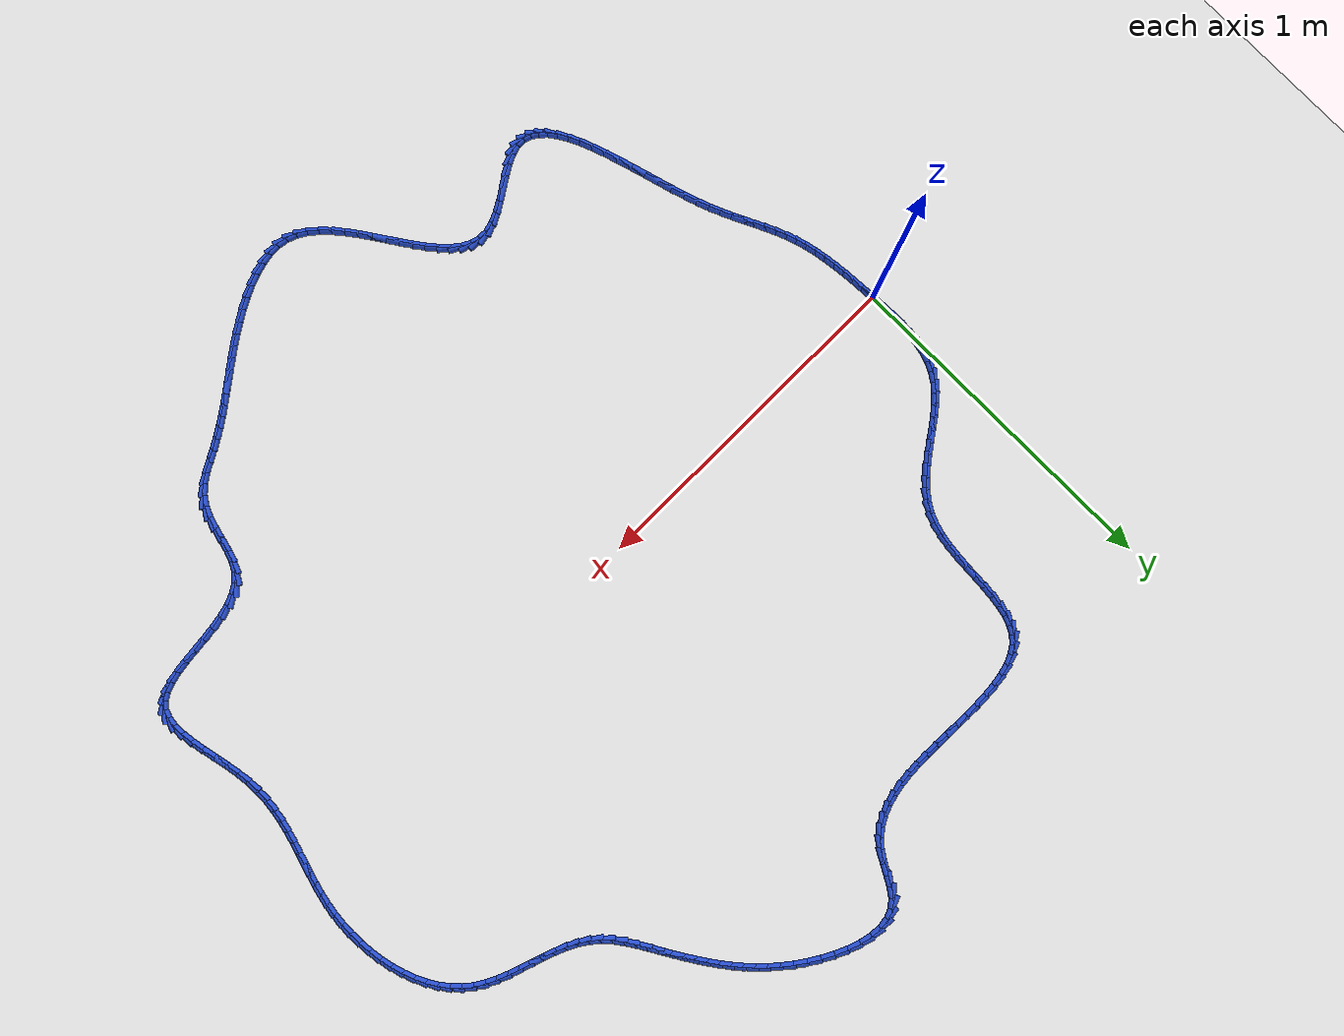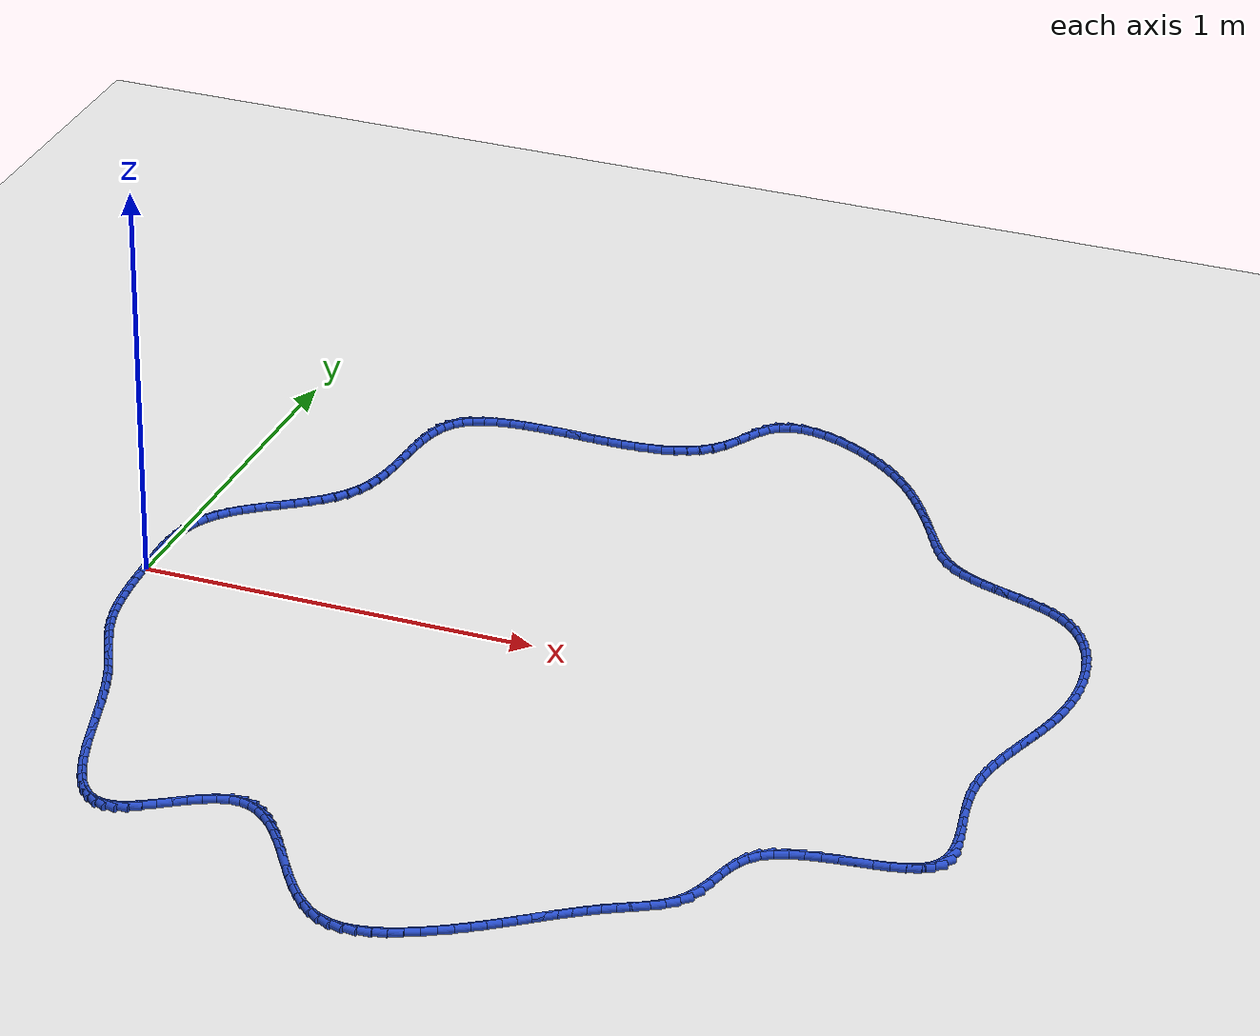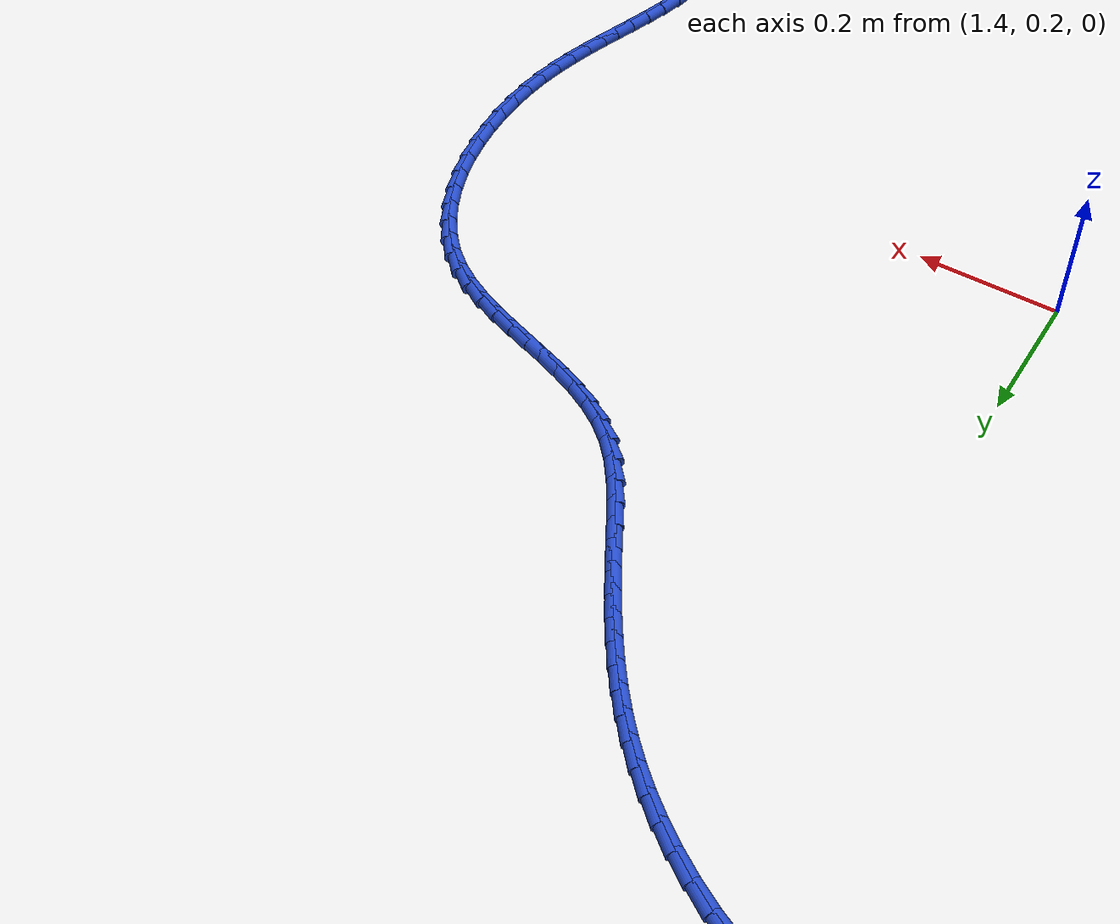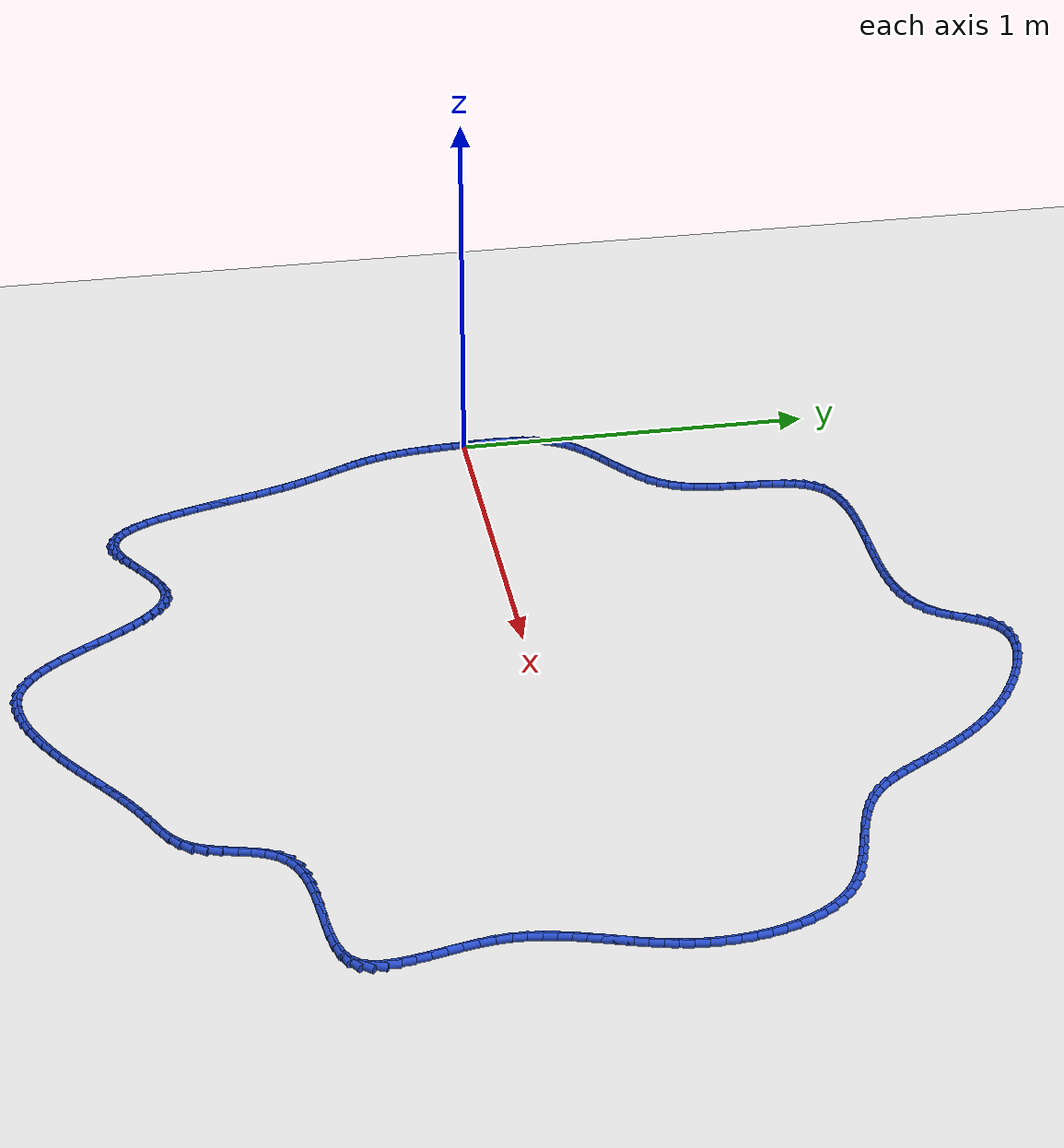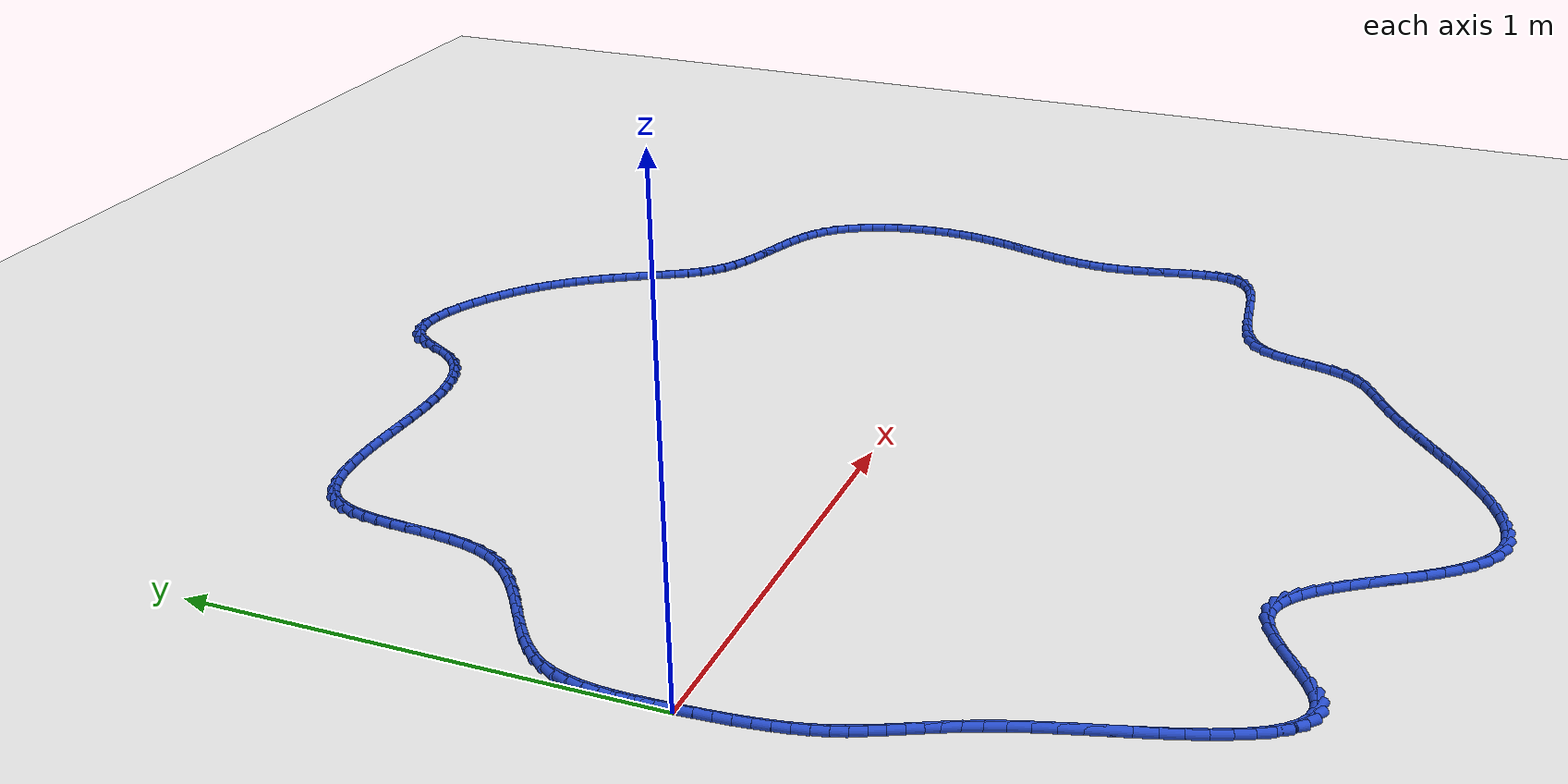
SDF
<sdf version="1.6">
 <world name="default">
  <light name="sun" type="directional">
   <pose>0 0 10 0 -0 0</pose>
   <diffuse>0.8 0.8 0.8 1</diffuse>
   <specular>0.2 0.2 0.2 1</specular>
   <attenuation>
    <range>1000</range>
    <constant>0.9</constant>
    <linear>0.01</linear>
    <quadratic>0.001</quadratic>
   </attenuation>
   <direction>-0.5 0.1 -0.9</direction>
  </light>
  <model name="ground_plane">
   <static>1</static>
   <link name="link">
    <collision name="collision">
     <geometry><plane><normal>0 0 1</normal><size>100 100</size></plane></geometry>
     <surface><friction><ode><mu>100</mu><mu2>50</mu2></ode></friction></surface>
    </collision>
    <visual name="visual">
     <cast_shadows>0</cast_shadows>
     <geometry><plane><normal>0 0 1</normal><size>100 100</size></plane></geometry>
     <material>
      <script><uri>file://media/materials/scripts/gazebo.material</uri><name>Gazebo/WhiteGlow</name></script>
     </material>
    </visual>
   </link>
  </model>
  <gravity>0 0 -9.8</gravity>
  <magnetic_field>6e-06 2.3e-05 -4.2e-05</magnetic_field>
  <atmosphere type="adiabatic"/>
  <physics name="default_physics" default="0" type="ode">
   <max_step_size>0.001</max_step_size>
   <real_time_factor>1</real_time_factor>
   <real_time_update_rate>1000</real_time_update_rate>
  </physics>
  <scene><ambient>0.4 0.4 0.4 1</ambient><background>0.7 0.7 0.7 1</background><shadows>1</shadows></scene>
  <spherical_coordinates>
   <surface_model>EARTH_WGS84</surface_model>
   <latitude_deg>0</latitude_deg>
   <longitude_deg>0</longitude_deg>
   <elevation>0</elevation>
   <heading_deg>0</heading_deg>
  </spherical_coordinates>
  <model name="line">
   <link name="link_0">
    <pose>6.071532165918825e-18 -2.0816681711721685e-17 0.01 0 1.57 -1.5283965037339577</pose>
    <collision name="collision">
     <geometry><cylinder><radius>0.01</radius><length>0.08</length></cylinder></geometry>
    </collision>
    <visual name="visual">
     <material>
      <script><name>Gazebo/Blue</name><uri>file://media/materials/scripts/gazebo.material</uri></script>
     </material>
     <geometry><cylinder><radius>0.01</radius><length>0.08</length></cylinder></geometry>
    </visual>
   </link>
   <link name="link_1">
    <pose>-0.001498879464508566 0.03532989167594646 0.01 0 1.57 -1.5470402116652142</pose>
    <collision name="collision">
     <geometry><cylinder><radius>0.01</radius><length>0.08</length></cylinder></geometry>
    </collision>
    <visual name="visual">
     <material>
      <script><name>Gazebo/Blue</name><uri>file://media/materials/scripts/gazebo.material</uri></script>
     </material>
     <geometry><cylinder><radius>0.01</radius><length>0.08</length></cylinder></geometry>
    </visual>
   </link>
   <link name="link_2">
    <pose>-0.0023387738931622644 0.07067811335036579 0.01 0 1.57 1.5620465766555596</pose>
    <collision name="collision">
     <geometry><cylinder><radius>0.01</radius><length>0.08</length></cylinder></geometry>
    </collision>
    <visual name="visual">
     <material>
      <script><name>Gazebo/Blue</name><uri>file://media/materials/scripts/gazebo.material</uri></script>
     </material>
     <geometry><cylinder><radius>0.01</radius><length>0.08</length></cylinder></geometry>
    </visual>
   </link>
   <link name="link_3">
    <pose>-0.0020322944470748576 0.10570444210294236 0.01 0 1.57 1.514395082861115</pose>
    <collision name="collision">
     <geometry><cylinder><radius>0.01</radius><length>0.08</length></cylinder></geometry>
    </collision>
    <visual name="visual">
     <material>
      <script><name>Gazebo/Blue</name><uri>file://media/materials/scripts/gazebo.material</uri></script>
     </material>
     <geometry><cylinder><radius>0.01</radius><length>0.08</length></cylinder></geometry>
    </visual>
   </link>
   <link name="link_4">
    <pose>-9.205228736011185e-05 0.14006865501336038 0.01 0 1.57 1.4496548437023833</pose>
    <collision name="collision">
     <geometry><cylinder><radius>0.01</radius><length>0.08</length></cylinder></geometry>
    </collision>
    <visual name="visual">
     <material>
      <script><name>Gazebo/Blue</name><uri>file://media/materials/scripts/gazebo.material</uri></script>
     </material>
     <geometry><cylinder><radius>0.01</radius><length>0.08</length></cylinder></geometry>
    </visual>
   </link>
   <link name="link_5">
    <pose>0.003969341424868209 0.17343052916130416 0.01 0 1.57 1.3654235661168286</pose>
    <collision name="collision">
     <geometry><cylinder><radius>0.01</radius><length>0.08</length></cylinder></geometry>
    </collision>
    <visual name="visual">
     <material>
      <script><name>Gazebo/Blue</name><uri>file://media/materials/scripts/gazebo.material</uri></script>
     </material>
     <geometry><cylinder><radius>0.01</radius><length>0.08</length></cylinder></geometry>
    </visual>
   </link>
   <link name="link_6">
    <pose>0.010639275528496344 0.20544984162645802 0.01 0 1.57 1.259354841588835</pose>
    <collision name="collision">
     <geometry><cylinder><radius>0.01</radius><length>0.08</length></cylinder></geometry>
    </collision>
    <visual name="visual">
     <material>
      <script><name>Gazebo/Blue</name><uri>file://media/materials/scripts/gazebo.material</uri></script>
     </material>
     <geometry><cylinder><radius>0.01</radius><length>0.08</length></cylinder></geometry>
    </visual>
   </link>
   <link name="link_7">
    <pose>0.020405138862410514 0.23578636948850618 0.01 0 1.57 1.130226139631336</pose>
    <collision name="collision">
     <geometry><cylinder><radius>0.01</radius><length>0.08</length></cylinder></geometry>
    </collision>
    <visual name="visual">
     <material>
      <script><name>Gazebo/Blue</name><uri>file://media/materials/scripts/gazebo.material</uri></script>
     </material>
     <geometry><cylinder><radius>0.01</radius><length>0.08</length></cylinder></geometry>
    </visual>
   </link>
   <link name="link_8">
    <pose>0.03375432026549696 0.26409988982713295 0.01 0 1.57 0.9833878627278883</pose>
    <collision name="collision">
     <geometry><cylinder><radius>0.01</radius><length>0.08</length></cylinder></geometry>
    </collision>
    <visual name="visual">
     <material>
      <script><name>Gazebo/Blue</name><uri>file://media/materials/scripts/gazebo.material</uri></script>
     </material>
     <geometry><cylinder><radius>0.01</radius><length>0.08</length></cylinder></geometry>
    </visual>
   </link>
   <link name="link_9">
    <pose>0.051075435489808696 0.290115038766558 0.01 0 1.57 0.852496347622651</pose>
    <collision name="collision">
     <geometry><cylinder><radius>0.01</radius><length>0.08</length></cylinder></geometry>
    </collision>
    <visual name="visual">
     <material>
      <script><name>Gazebo/Blue</name><uri>file://media/materials/scripts/gazebo.material</uri></script>
     </material>
     <geometry><cylinder><radius>0.01</radius><length>0.08</length></cylinder></geometry>
    </visual>
   </link>
   <link name="link_10">
    <pose>0.07199954562878354 0.3140538983741864 0.01 0 1.57 0.7530468306794879</pose>
    <collision name="collision">
     <geometry><cylinder><radius>0.01</radius><length>0.08</length></cylinder></geometry>
    </collision>
    <visual name="visual">
     <material>
      <script><name>Gazebo/Blue</name><uri>file://media/materials/scripts/gazebo.material</uri></script>
     </material>
     <geometry><cylinder><radius>0.01</radius><length>0.08</length></cylinder></geometry>
    </visual>
   </link>
   <link name="link_11">
    <pose>0.09580708123976286 0.3363687911835788 0.01 0 1.57 0.6833430598227593</pose>
    <collision name="collision">
     <geometry><cylinder><radius>0.01</radius><length>0.08</length></cylinder></geometry>
    </collision>
    <visual name="visual">
     <material>
      <script><name>Gazebo/Blue</name><uri>file://media/materials/scripts/gazebo.material</uri></script>
     </material>
     <geometry><cylinder><radius>0.01</radius><length>0.08</length></cylinder></geometry>
    </visual>
   </link>
   <link name="link_12">
    <pose>0.12177656684679818 0.35751329131921045 0.01 0 1.57 0.6404637598815272</pose>
    <collision name="collision">
     <geometry><cylinder><radius>0.01</radius><length>0.08</length></cylinder></geometry>
    </collision>
    <visual name="visual">
     <material>
      <script><name>Gazebo/Blue</name><uri>file://media/materials/scripts/gazebo.material</uri></script>
     </material>
     <geometry><cylinder><radius>0.01</radius><length>0.08</length></cylinder></geometry>
    </visual>
   </link>
   <link name="link_13">
    <pose>0.14918652697394097 0.377940972905556 0.01 0 1.57 0.6219499275188383</pose>
    <collision name="collision">
     <geometry><cylinder><radius>0.01</radius><length>0.08</length></cylinder></geometry>
    </collision>
    <visual name="visual">
     <material>
      <script><name>Gazebo/Blue</name><uri>file://media/materials/scripts/gazebo.material</uri></script>
     </material>
     <geometry><cylinder><radius>0.01</radius><length>0.08</length></cylinder></geometry>
    </visual>
   </link>
   <link name="link_14">
    <pose>0.17731548614524287 0.3981054100670906 0.01 0 1.57 0.6264469530278278</pose>
    <collision name="collision">
     <geometry><cylinder><radius>0.01</radius><length>0.08</length></cylinder></geometry>
    </collision>
    <visual name="visual">
     <material>
      <script><name>Gazebo/Blue</name><uri>file://media/materials/scripts/gazebo.material</uri></script>
     </material>
     <geometry><cylinder><radius>0.01</radius><length>0.08</length></cylinder></geometry>
    </visual>
   </link>
   <link name="link_15">
    <pose>0.20544196888475533 0.418460176928289 0.01 0 1.57 0.6538543119953212</pose>
    <collision name="collision">
     <geometry><cylinder><radius>0.01</radius><length>0.08</length></cylinder></geometry>
    </collision>
    <visual name="visual">
     <material>
      <script><name>Gazebo/Blue</name><uri>file://media/materials/scripts/gazebo.material</uri></script>
     </material>
     <geometry><cylinder><radius>0.01</radius><length>0.08</length></cylinder></geometry>
    </visual>
   </link>
   <link name="link_16">
    <pose>0.2328444997165299 0.4394588476136263 0.01 0 1.57 0.7052229768547227</pose>
    <collision name="collision">
     <geometry><cylinder><radius>0.01</radius><length>0.08</length></cylinder></geometry>
    </collision>
    <visual name="visual">
     <material>
      <script><name>Gazebo/Blue</name><uri>file://media/materials/scripts/gazebo.material</uri></script>
     </material>
     <geometry><cylinder><radius>0.01</radius><length>0.08</length></cylinder></geometry>
    </visual>
   </link>
   <link name="link_17">
    <pose>0.25880160316461814 0.46155499624757723 0.01 0 1.57 0.7823836760023695</pose>
    <collision name="collision">
     <geometry><cylinder><radius>0.01</radius><length>0.08</length></cylinder></geometry>
    </collision>
    <visual name="visual">
     <material>
      <script><name>Gazebo/Blue</name><uri>file://media/materials/scripts/gazebo.material</uri></script>
     </material>
     <geometry><cylinder><radius>0.01</radius><length>0.08</length></cylinder></geometry>
    </visual>
   </link>
   <link name="link_18">
    <pose>0.28259180375307147 0.4852021969546167 0.01 0 1.57 0.887079197893865</pose>
    <collision name="collision">
     <geometry><cylinder><radius>0.01</radius><length>0.08</length></cylinder></geometry>
    </collision>
    <visual name="visual">
     <material>
      <script><name>Gazebo/Blue</name><uri>file://media/materials/scripts/gazebo.material</uri></script>
     </material>
     <geometry><cylinder><radius>0.01</radius><length>0.08</length></cylinder></geometry>
    </visual>
   </link>
   <link name="link_19">
    <pose>0.30349362600594154 0.5108540238592197 0.01 0 1.57 1.0193093350753561</pose>
    <collision name="collision">
     <geometry><cylinder><radius>0.01</radius><length>0.08</length></cylinder></geometry>
    </collision>
    <visual name="visual">
     <material>
      <script><name>Gazebo/Blue</name><uri>file://media/materials/scripts/gazebo.material</uri></script>
     </material>
     <geometry><cylinder><radius>0.01</radius><length>0.08</length></cylinder></geometry>
    </visual>
   </link>
   <link name="link_20">
    <pose>0.3207855944472799 0.5389640510858612 0.01 0 1.57 1.1677564541266574</pose>
    <collision name="collision">
     <geometry><cylinder><radius>0.01</radius><length>0.08</length></cylinder></geometry>
    </collision>
    <visual name="visual">
     <material>
      <script><name>Gazebo/Blue</name><uri>file://media/materials/scripts/gazebo.material</uri></script>
     </material>
     <geometry><cylinder><radius>0.01</radius><length>0.08</length></cylinder></geometry>
    </visual>
   </link>
   <link name="link_21">
    <pose>0.3339505472622256 0.5698400742210961 0.01 0 1.57 1.2925705500301454</pose>
    <collision name="collision">
     <geometry><cylinder><radius>0.01</radius><length>0.08</length></cylinder></geometry>
    </collision>
    <visual name="visual">
     <material>
      <script><name>Gazebo/Blue</name><uri>file://media/materials/scripts/gazebo.material</uri></script>
     </material>
     <geometry><cylinder><radius>0.01</radius><length>0.08</length></cylinder></geometry>
    </visual>
   </link>
   <link name="link_22">
    <pose>0.34344860917789005 0.6030925913606555 0.01 0 1.57 1.3850402392008254</pose>
    <collision name="collision">
     <geometry><cylinder><radius>0.01</radius><length>0.08</length></cylinder></geometry>
    </collision>
    <visual name="visual">
     <material>
      <script><name>Gazebo/Blue</name><uri>file://media/materials/scripts/gazebo.material</uri></script>
     </material>
     <geometry><cylinder><radius>0.01</radius><length>0.08</length></cylinder></geometry>
    </visual>
   </link>
   <link name="link_23">
    <pose>0.35003177197942226 0.6381238523962037 0.01 0 1.57 1.4493305061179154</pose>
    <collision name="collision">
     <geometry><cylinder><radius>0.01</radius><length>0.08</length></cylinder></geometry>
    </collision>
    <visual name="visual">
     <material>
      <script><name>Gazebo/Blue</name><uri>file://media/materials/scripts/gazebo.material</uri></script>
     </material>
     <geometry><cylinder><radius>0.01</radius><length>0.08</length></cylinder></geometry>
    </visual>
   </link>
   <link name="link_24">
    <pose>0.35445207915239474 0.674336070330966 0.01 0 1.57 1.4891879721612624</pose>
    <collision name="collision">
     <geometry><cylinder><radius>0.01</radius><length>0.08</length></cylinder></geometry>
    </collision>
    <visual name="visual">
     <material>
      <script><name>Gazebo/Blue</name><uri>file://media/materials/scripts/gazebo.material</uri></script>
     </material>
     <geometry><cylinder><radius>0.01</radius><length>0.08</length></cylinder></geometry>
    </visual>
   </link>
   <link name="link_25">
    <pose>0.35746157418237945 0.7111314581681671 0.01 0 1.57 1.5069713046771587</pose>
    <collision name="collision">
     <geometry><cylinder><radius>0.01</radius><length>0.08</length></cylinder></geometry>
    </collision>
    <visual name="visual">
     <material>
      <script><name>Gazebo/Blue</name><uri>file://media/materials/scripts/gazebo.material</uri></script>
     </material>
     <geometry><cylinder><radius>0.01</radius><length>0.08</length></cylinder></geometry>
    </visual>
   </link>
   <link name="link_26">
    <pose>0.3598123005549488 0.7479122289110327 0.01 0 1.57 1.5033260001918445</pose>
    <collision name="collision">
     <geometry><cylinder><radius>0.01</radius><length>0.08</length></cylinder></geometry>
    </collision>
    <visual name="visual">
     <material>
      <script><name>Gazebo/Blue</name><uri>file://media/materials/scripts/gazebo.material</uri></script>
     </material>
     <geometry><cylinder><radius>0.01</radius><length>0.08</length></cylinder></geometry>
    </visual>
   </link>
   <link name="link_27">
    <pose>0.3622563017556751 0.7840805955627879 0.01 0 1.57 1.476979547674237</pose>
    <collision name="collision">
     <geometry><cylinder><radius>0.01</radius><length>0.08</length></cylinder></geometry>
    </collision>
    <visual name="visual">
     <material>
      <script><name>Gazebo/Blue</name><uri>file://media/materials/scripts/gazebo.material</uri></script>
     </material>
     <geometry><cylinder><radius>0.01</radius><length>0.08</length></cylinder></geometry>
    </visual>
   </link>
   <link name="link_28">
    <pose>0.3655456212701304 0.8190387711266578 0.01 0 1.57 1.4244400278740543</pose>
    <collision name="collision">
     <geometry><cylinder><radius>0.01</radius><length>0.08</length></cylinder></geometry>
    </collision>
    <visual name="visual">
     <material>
      <script><name>Gazebo/Blue</name><uri>file://media/materials/scripts/gazebo.material</uri></script>
     </material>
     <geometry><cylinder><radius>0.01</radius><length>0.08</length></cylinder></geometry>
    </visual>
   </link>
   <link name="link_29">
    <pose>0.37043230258388704 0.8521889686058675 0.01 0 1.57 1.3396408615475375</pose>
    <collision name="collision">
     <geometry><cylinder><radius>0.01</radius><length>0.08</length></cylinder></geometry>
    </collision>
    <visual name="visual">
     <material>
      <script><name>Gazebo/Blue</name><uri>file://media/materials/scripts/gazebo.material</uri></script>
     </material>
     <geometry><cylinder><radius>0.01</radius><length>0.08</length></cylinder></geometry>
    </visual>
   </link>
   <link name="link_30">
    <pose>0.37766838918251716 0.8829334010036423 0.01 0 1.57 1.2140908023654706</pose>
    <collision name="collision">
     <geometry><cylinder><radius>0.01</radius><length>0.08</length></cylinder></geometry>
    </collision>
    <visual name="visual">
     <material>
      <script><name>Gazebo/Blue</name><uri>file://media/materials/scripts/gazebo.material</uri></script>
     </material>
     <geometry><cylinder><radius>0.01</radius><length>0.08</length></cylinder></geometry>
    </visual>
   </link>
   <link name="link_31">
    <pose>0.388005924551593 0.9106742813232072 0.01 0 1.57 1.03934013480232</pose>
    <collision name="collision">
     <geometry><cylinder><radius>0.01</radius><length>0.08</length></cylinder></geometry>
    </collision>
    <visual name="visual">
     <material>
      <script><name>Gazebo/Blue</name><uri>file://media/materials/scripts/gazebo.material</uri></script>
     </material>
     <geometry><cylinder><radius>0.01</radius><length>0.08</length></cylinder></geometry>
    </visual>
   </link>
   <link name="link_32">
    <pose>0.40219695217668694 0.9348138225677877 0.01 0 1.57 0.815283021354379</pose>
    <collision name="collision">
     <geometry><cylinder><radius>0.01</radius><length>0.08</length></cylinder></geometry>
    </collision>
    <visual name="visual">
     <material>
      <script><name>Gazebo/Blue</name><uri>file://media/materials/scripts/gazebo.material</uri></script>
     </material>
     <geometry><cylinder><radius>0.01</radius><length>0.08</length></cylinder></geometry>
    </visual>
   </link>
   <link name="link_33">
    <pose>0.42098562203401996 0.9547604355940542 0.01 0 1.57 0.5829530819946772</pose>
    <collision name="collision">
     <geometry><cylinder><radius>0.01</radius><length>0.08</length></cylinder></geometry>
    </collision>
    <visual name="visual">
     <material>
      <script><name>Gazebo/Blue</name><uri>file://media/materials/scripts/gazebo.material</uri></script>
     </material>
     <geometry><cylinder><radius>0.01</radius><length>0.08</length></cylinder></geometry>
    </visual>
   </link>
   <link name="link_34">
    <pose>0.4445972717253716 0.970329894184308 0.01 0 1.57 0.3967951697159996</pose>
    <collision name="collision">
     <geometry><cylinder><radius>0.01</radius><length>0.08</length></cylinder></geometry>
    </collision>
    <visual name="visual">
     <material>
      <script><name>Gazebo/Blue</name><uri>file://media/materials/scripts/gazebo.material</uri></script>
     </material>
     <geometry><cylinder><radius>0.01</radius><length>0.08</length></cylinder></geometry>
    </visual>
   </link>
   <link name="link_35">
    <pose>0.47242595205525834 0.9819906848132454 0.01 0 1.57 0.25808028765324126</pose>
    <collision name="collision">
     <geometry><cylinder><radius>0.01</radius><length>0.08</length></cylinder></geometry>
    </collision>
    <visual name="visual">
     <material>
      <script><name>Gazebo/Blue</name><uri>file://media/materials/scripts/gazebo.material</uri></script>
     </material>
     <geometry><cylinder><radius>0.01</radius><length>0.08</length></cylinder></geometry>
    </visual>
   </link>
   <link name="link_36">
    <pose>0.5037909379305072 0.9902700067580135 0.01 0 1.57 0.15722351294328715</pose>
    <collision name="collision">
     <geometry><cylinder><radius>0.01</radius><length>0.08</length></cylinder></geometry>
    </collision>
    <visual name="visual">
     <material>
      <script><name>Gazebo/Blue</name><uri>file://media/materials/scripts/gazebo.material</uri></script>
     </material>
     <geometry><cylinder><radius>0.01</radius><length>0.08</length></cylinder></geometry>
    </visual>
   </link>
   <link name="link_37">
    <pose>0.5380115042579448 0.9956950592957591 0.01 0 1.57 0.08491542475617707</pose>
    <collision name="collision">
     <geometry><cylinder><radius>0.01</radius><length>0.08</length></cylinder></geometry>
    </collision>
    <visual name="visual">
     <material>
      <script><name>Gazebo/Blue</name><uri>file://media/materials/scripts/gazebo.material</uri></script>
     </material>
     <geometry><cylinder><radius>0.01</radius><length>0.08</length></cylinder></geometry>
    </visual>
   </link>
   <link name="link_38">
    <pose>0.5744069259443979 0.9987930417036291 0.01 0 1.57 0.034247013977091297</pose>
    <collision name="collision">
     <geometry><cylinder><radius>0.01</radius><length>0.08</length></cylinder></geometry>
    </collision>
    <visual name="visual">
     <material>
      <script><name>Gazebo/Blue</name><uri>file://media/materials/scripts/gazebo.material</uri></script>
     </material>
     <geometry><cylinder><radius>0.01</radius><length>0.08</length></cylinder></geometry>
    </visual>
   </link>
   <link name="link_39">
    <pose>0.612296477896694 1.0000911532587708 0.01 0 1.57 0.0006573134919392366</pose>
    <collision name="collision">
     <geometry><cylinder><radius>0.01</radius><length>0.08</length></cylinder></geometry>
    </collision>
    <visual name="visual">
     <material>
      <script><name>Gazebo/Blue</name><uri>file://media/materials/scripts/gazebo.material</uri></script>
     </material>
     <geometry><cylinder><radius>0.01</radius><length>0.08</length></cylinder></geometry>
    </visual>
   </link>
   <link name="link_40">
    <pose>0.6509994350216592 1.000116593238331 0.01 0 1.57 -0.018804038210180195</pose>
    <collision name="collision">
     <geometry><cylinder><radius>0.01</radius><length>0.08</length></cylinder></geometry>
    </collision>
    <visual name="visual">
     <material>
      <script><name>Gazebo/Blue</name><uri>file://media/materials/scripts/gazebo.material</uri></script>
     </material>
     <geometry><cylinder><radius>0.01</radius><length>0.08</length></cylinder></geometry>
    </visual>
   </link>
   <link name="link_41">
    <pose>0.6898808395212194 0.9993853796366999 0.01 0 1.57 -0.02692615971927765</pose>
    <collision name="collision">
     <geometry><cylinder><radius>0.01</radius><length>0.08</length></cylinder></geometry>
    </collision>
    <visual name="visual">
     <material>
      <script><name>Gazebo/Blue</name><uri>file://media/materials/scripts/gazebo.material</uri></script>
     </material>
     <geometry><cylinder><radius>0.01</radius><length>0.08</length></cylinder></geometry>
    </visual>
   </link>
   <link name="link_42">
    <pose>0.7285957203892466 0.9983426845678293 0.01 0 1.57 -0.024440593419900875</pose>
    <collision name="collision">
     <geometry><cylinder><radius>0.01</radius><length>0.08</length></cylinder></geometry>
    </collision>
    <visual name="visual">
     <material>
      <script><name>Gazebo/Blue</name><uri>file://media/materials/scripts/gazebo.material</uri></script>
     </material>
     <geometry><cylinder><radius>0.01</radius><length>0.08</length></cylinder></geometry>
    </visual>
   </link>
   <link name="link_43">
    <pose>0.7669123366913767 0.9974060172163626 0.01 0 1.57 -0.01096342779789743</pose>
    <collision name="collision">
     <geometry><cylinder><radius>0.01</radius><length>0.08</length></cylinder></geometry>
    </collision>
    <visual name="visual">
     <material>
      <script><name>Gazebo/Blue</name><uri>file://media/materials/scripts/gazebo.material</uri></script>
     </material>
     <geometry><cylinder><radius>0.01</radius><length>0.08</length></cylinder></geometry>
    </visual>
   </link>
   <link name="link_44">
    <pose>0.8045992069474439 0.9969928233803969 0.01 0 1.57 0.014329399799486206</pose>
    <collision name="collision">
     <geometry><cylinder><radius>0.01</radius><length>0.08</length></cylinder></geometry>
    </collision>
    <visual name="visual">
     <material>
      <script><name>Gazebo/Blue</name><uri>file://media/materials/scripts/gazebo.material</uri></script>
     </material>
     <geometry><cylinder><radius>0.01</radius><length>0.08</length></cylinder></geometry>
    </visual>
   </link>
   <link name="link_45">
    <pose>0.8414248496772821 0.9975205488580298 0.01 0 1.57 0.05273403941169539</pose>
    <collision name="collision">
     <geometry><cylinder><radius>0.01</radius><length>0.08</length></cylinder></geometry>
    </collision>
    <visual name="visual">
     <material>
      <script><name>Gazebo/Blue</name><uri>file://media/materials/scripts/gazebo.material</uri></script>
     </material>
     <geometry><cylinder><radius>0.01</radius><length>0.08</length></cylinder></geometry>
    </visual>
   </link>
   <link name="link_46">
    <pose>0.8771577834007256 0.9994066394473585 0.01 0 1.57 0.10602450073112599</pose>
    <collision name="collision">
     <geometry><cylinder><radius>0.01</radius><length>0.08</length></cylinder></geometry>
    </collision>
    <visual name="visual">
     <material>
      <script><name>Gazebo/Blue</name><uri>file://media/materials/scripts/gazebo.material</uri></script>
     </material>
     <geometry><cylinder><radius>0.01</radius><length>0.08</length></cylinder></geometry>
    </visual>
   </link>
   <link name="link_47">
    <pose>0.9115665266376078 1.0030685409464801 0.01 0 1.57 0.17637074032755815</pose>
    <collision name="collision">
     <geometry><cylinder><radius>0.01</radius><length>0.08</length></cylinder></geometry>
    </collision>
    <visual name="visual">
     <material>
      <script><name>Gazebo/Blue</name><uri>file://media/materials/scripts/gazebo.material</uri></script>
     </material>
     <geometry><cylinder><radius>0.01</radius><length>0.08</length></cylinder></geometry>
    </visual>
   </link>
   <link name="link_48">
    <pose>0.9444195979077632 1.0089236991534922 0.01 0 1.57 0.26605242752533</pose>
    <collision name="collision">
     <geometry><cylinder><radius>0.01</radius><length>0.08</length></cylinder></geometry>
    </collision>
    <visual name="visual">
     <material>
      <script><name>Gazebo/Blue</name><uri>file://media/materials/scripts/gazebo.material</uri></script>
     </material>
     <geometry><cylinder><radius>0.01</radius><length>0.08</length></cylinder></geometry>
    </visual>
   </link>
   <link name="link_49">
    <pose>0.9754855157310255 1.0173895598664922 0.01 0 1.57 0.3767939684651764</pose>
    <collision name="collision">
     <geometry><cylinder><radius>0.01</radius><length>0.08</length></cylinder></geometry>
    </collision>
    <visual name="visual">
     <material>
      <script><name>Gazebo/Blue</name><uri>file://media/materials/scripts/gazebo.material</uri></script>
     </material>
     <geometry><cylinder><radius>0.01</radius><length>0.08</length></cylinder></geometry>
    </visual>
   </link>
   <link name="link_50">
    <pose>1.0045327986272288 1.0288835688835767 0.01 0 1.57 0.5085883310137791</pose>
    <collision name="collision">
     <geometry><cylinder><radius>0.01</radius><length>0.08</length></cylinder></geometry>
    </collision>
    <visual name="visual">
     <material>
      <script><name>Gazebo/Blue</name><uri>file://media/materials/scripts/gazebo.material</uri></script>
     </material>
     <geometry><cylinder><radius>0.01</radius><length>0.08</length></cylinder></geometry>
    </visual>
   </link>
   <link name="link_51">
    <pose>1.0313299651162073 1.0438231720028437 0.01 0 1.57 0.6582320225758695</pose>
    <collision name="collision">
     <geometry><cylinder><radius>0.01</radius><length>0.08</length></cylinder></geometry>
    </collision>
    <visual name="visual">
     <material>
      <script><name>Gazebo/Blue</name><uri>file://media/materials/scripts/gazebo.material</uri></script>
     </material>
     <geometry><cylinder><radius>0.01</radius><length>0.08</length></cylinder></geometry>
    </visual>
   </link>
   <link name="link_52">
    <pose>1.0556455337177948 1.06262581502239 0.01 0 1.57 0.818520631951938</pose>
    <collision name="collision">
     <geometry><cylinder><radius>0.01</radius><length>0.08</length></cylinder></geometry>
    </collision>
    <visual name="visual">
     <material>
      <script><name>Gazebo/Blue</name><uri>file://media/materials/scripts/gazebo.material</uri></script>
     </material>
     <geometry><cylinder><radius>0.01</radius><length>0.08</length></cylinder></geometry>
    </visual>
   </link>
   <link name="link_53">
    <pose>1.0772480229518255 1.0857089437403136 0.01 0 1.57 0.974031176421292</pose>
    <collision name="collision">
     <geometry><cylinder><radius>0.01</radius><length>0.08</length></cylinder></geometry>
    </collision>
    <visual name="visual">
     <material>
      <script><name>Gazebo/Blue</name><uri>file://media/materials/scripts/gazebo.material</uri></script>
     </material>
     <geometry><cylinder><radius>0.01</radius><length>0.08</length></cylinder></geometry>
    </visual>
   </link>
   <link name="link_54">
    <pose>1.0960052413835928 1.1133175147934362 0.01 0 1.57 1.0609677081710676</pose>
    <collision name="collision">
     <geometry><cylinder><radius>0.01</radius><length>0.08</length></cylinder></geometry>
    </collision>
    <visual name="visual">
     <material>
      <script><name>Gazebo/Blue</name><uri>file://media/materials/scripts/gazebo.material</uri></script>
     </material>
     <geometry><cylinder><radius>0.01</radius><length>0.08</length></cylinder></geometry>
    </visual>
   </link>
   <link name="link_55">
    <pose>1.1129641025677646 1.1436481140102965 0.01 0 1.57 1.0544158243072181</pose>
    <collision name="collision">
     <geometry><cylinder><radius>0.01</radius><length>0.08</length></cylinder></geometry>
    </collision>
    <visual name="visual">
     <material>
      <script><name>Gazebo/Blue</name><uri>file://media/materials/scripts/gazebo.material</uri></script>
     </material>
     <geometry><cylinder><radius>0.01</radius><length>0.08</length></cylinder></geometry>
    </visual>
   </link>
   <link name="link_56">
    <pose>1.1299442054143685 1.1735549988091838 0.01 0 1.57 0.94957662426408</pose>
    <collision name="collision">
     <geometry><cylinder><radius>0.01</radius><length>0.08</length></cylinder></geometry>
    </collision>
    <visual name="visual">
     <material>
      <script><name>Gazebo/Blue</name><uri>file://media/materials/scripts/gazebo.material</uri></script>
     </material>
     <geometry><cylinder><radius>0.01</radius><length>0.08</length></cylinder></geometry>
    </visual>
   </link>
   <link name="link_57">
    <pose>1.1487785756594064 1.199869101189001 0.01 0 1.57 0.7165296196188103</pose>
    <collision name="collision">
     <geometry><cylinder><radius>0.01</radius><length>0.08</length></cylinder></geometry>
    </collision>
    <visual name="visual">
     <material>
      <script><name>Gazebo/Blue</name><uri>file://media/materials/scripts/gazebo.material</uri></script>
     </material>
     <geometry><cylinder><radius>0.01</radius><length>0.08</length></cylinder></geometry>
    </visual>
   </link>
   <link name="link_58">
    <pose>1.171273794002101 1.2194612338461794 0.01 0 1.57 0.4020228922208706</pose>
    <collision name="collision">
     <geometry><cylinder><radius>0.01</radius><length>0.08</length></cylinder></geometry>
    </collision>
    <visual name="visual">
     <material>
      <script><name>Gazebo/Blue</name><uri>file://media/materials/scripts/gazebo.material</uri></script>
     </material>
     <geometry><cylinder><radius>0.01</radius><length>0.08</length></cylinder></geometry>
    </visual>
   </link>
   <link name="link_59">
    <pose>1.19812526181939 1.2308779343709386 0.01 0 1.57 0.13208137055408006</pose>
    <collision name="collision">
     <geometry><cylinder><radius>0.01</radius><length>0.08</length></cylinder></geometry>
    </collision>
    <visual name="visual">
     <material>
      <script><name>Gazebo/Blue</name><uri>file://media/materials/scripts/gazebo.material</uri></script>
     </material>
     <geometry><cylinder><radius>0.01</radius><length>0.08</length></cylinder></geometry>
    </visual>
   </link>
   <link name="link_60">
    <pose>1.2285348976816137 1.234918001772757 0.01 0 1.57 -0.07183834856826378</pose>
    <collision name="collision">
     <geometry><cylinder><radius>0.01</radius><length>0.08</length></cylinder></geometry>
    </collision>
    <visual name="visual">
     <material>
      <script><name>Gazebo/Blue</name><uri>file://media/materials/scripts/gazebo.material</uri></script>
     </material>
     <geometry><cylinder><radius>0.01</radius><length>0.08</length></cylinder></geometry>
    </visual>
   </link>
   <link name="link_61">
    <pose>1.261599612649631 1.2325385926674397 0.01 0 1.57 -0.22153232378098164</pose>
    <collision name="collision">
     <geometry><cylinder><radius>0.01</radius><length>0.08</length></cylinder></geometry>
    </collision>
    <visual name="visual">
     <material>
      <script><name>Gazebo/Blue</name><uri>file://media/materials/scripts/gazebo.material</uri></script>
     </material>
     <geometry><cylinder><radius>0.01</radius><length>0.08</length></cylinder></geometry>
    </visual>
   </link>
   <link name="link_62">
    <pose>1.296416317784299 1.2246968636707902 0.01 0 1.57 -0.3332719793162574</pose>
    <collision name="collision">
     <geometry><cylinder><radius>0.01</radius><length>0.08</length></cylinder></geometry>
    </collision>
    <visual name="visual">
     <material>
      <script><name>Gazebo/Blue</name><uri>file://media/materials/scripts/gazebo.material</uri></script>
     </material>
     <geometry><cylinder><radius>0.01</radius><length>0.08</length></cylinder></geometry>
    </visual>
   </link>
   <link name="link_63">
    <pose>1.3320819241464772 1.2123499713986137 0.01 0 1.57 -0.41980840459464075</pose>
    <collision name="collision">
     <geometry><cylinder><radius>0.01</radius><length>0.08</length></cylinder></geometry>
    </collision>
    <visual name="visual">
     <material>
      <script><name>Gazebo/Blue</name><uri>file://media/materials/scripts/gazebo.material</uri></script>
     </material>
     <geometry><cylinder><radius>0.01</radius><length>0.08</length></cylinder></geometry>
    </visual>
   </link>
   <link name="link_64">
    <pose>1.3676933427970226 1.1964550724667147 0.01 0 1.57 -0.490036851172639</pose>
    <collision name="collision">
     <geometry><cylinder><radius>0.01</radius><length>0.08</length></cylinder></geometry>
    </collision>
    <visual name="visual">
     <material>
      <script><name>Gazebo/Blue</name><uri>file://media/materials/scripts/gazebo.material</uri></script>
     </material>
     <geometry><cylinder><radius>0.01</radius><length>0.08</length></cylinder></geometry>
    </visual>
   </link>
   <link name="link_65">
    <pose>1.4023474847967938 1.1779693234908963 0.01 0 1.57 -0.5503059588106858</pose>
    <collision name="collision">
     <geometry><cylinder><radius>0.01</radius><length>0.08</length></cylinder></geometry>
    </collision>
    <visual name="visual">
     <material>
      <script><name>Gazebo/Blue</name><uri>file://media/materials/scripts/gazebo.material</uri></script>
     </material>
     <geometry><cylinder><radius>0.01</radius><length>0.08</length></cylinder></geometry>
    </visual>
   </link>
   <link name="link_66">
    <pose>1.4351431427489032 1.1578483261101857 0.01 0 1.57 -0.6066670999259629</pose>
    <collision name="collision">
     <geometry><cylinder><radius>0.01</radius><length>0.08</length></cylinder></geometry>
    </collision>
    <visual name="visual">
     <material>
      <script><name>Gazebo/Blue</name><uri>file://media/materials/scripts/gazebo.material</uri></script>
     </material>
     <geometry><cylinder><radius>0.01</radius><length>0.08</length></cylinder></geometry>
    </visual>
   </link>
   <link name="link_67">
    <pose>1.4655067152942505 1.1367769361008409 0.01 0 1.57 -0.6630956493104154</pose>
    <collision name="collision">
     <geometry><cylinder><radius>0.01</radius><length>0.08</length></cylinder></geometry>
    </collision>
    <visual name="visual">
     <material>
      <script><name>Gazebo/Blue</name><uri>file://media/materials/scripts/gazebo.material</uri></script>
     </material>
     <geometry><cylinder><radius>0.01</radius><length>0.08</length></cylinder></geometry>
    </visual>
   </link>
   <link name="link_68">
    <pose>1.4935632908578145 1.1148625859117636 0.01 0 1.57 -0.7189431250171929</pose>
    <collision name="collision">
     <geometry><cylinder><radius>0.01</radius><length>0.08</length></cylinder></geometry>
    </collision>
    <visual name="visual">
     <material>
      <script><name>Gazebo/Blue</name><uri>file://media/materials/scripts/gazebo.material</uri></script>
     </material>
     <geometry><cylinder><radius>0.01</radius><length>0.08</length></cylinder></geometry>
    </visual>
   </link>
   <link name="link_69">
    <pose>1.519527691899074 1.0921385484349884 0.01 0 1.57 -0.7730720822306014</pose>
    <collision name="collision">
     <geometry><cylinder><radius>0.01</radius><length>0.08</length></cylinder></geometry>
    </collision>
    <visual name="visual">
     <material>
      <script><name>Gazebo/Blue</name><uri>file://media/materials/scripts/gazebo.material</uri></script>
     </material>
     <geometry><cylinder><radius>0.01</radius><length>0.08</length></cylinder></geometry>
    </visual>
   </link>
   <link name="link_70">
    <pose>1.543614740877509 1.0686380965625477 0.01 0 1.57 -0.8243573896777183</pose>
    <collision name="collision">
     <geometry><cylinder><radius>0.01</radius><length>0.08</length></cylinder></geometry>
    </collision>
    <visual name="visual">
     <material>
      <script><name>Gazebo/Blue</name><uri>file://media/materials/scripts/gazebo.material</uri></script>
     </material>
     <geometry><cylinder><radius>0.01</radius><length>0.08</length></cylinder></geometry>
    </visual>
   </link>
   <link name="link_71">
    <pose>1.5660392602525983 1.0443945031864756 0.01 0 1.57 -0.8717629368289707</pose>
    <collision name="collision">
     <geometry><cylinder><radius>0.01</radius><length>0.08</length></cylinder></geometry>
    </collision>
    <visual name="visual">
     <material>
      <script><name>Gazebo/Blue</name><uri>file://media/materials/scripts/gazebo.material</uri></script>
     </material>
     <geometry><cylinder><radius>0.01</radius><length>0.08</length></cylinder></geometry>
    </visual>
   </link>
   <link name="link_72">
    <pose>1.5870160724838207 1.0194410411988042 0.01 0 1.57 -0.9144025098020466</pose>
    <collision name="collision">
     <geometry><cylinder><radius>0.01</radius><length>0.08</length></cylinder></geometry>
    </collision>
    <visual name="visual">
     <material>
      <script><name>Gazebo/Blue</name><uri>file://media/materials/scripts/gazebo.material</uri></script>
     </material>
     <geometry><cylinder><radius>0.01</radius><length>0.08</length></cylinder></geometry>
    </visual>
   </link>
   <link name="link_73">
    <pose>1.6067600000306557 0.9938109834915674 0.01 0 1.57 -0.9515767544803237</pose>
    <collision name="collision">
     <geometry><cylinder><radius>0.01</radius><length>0.08</length></cylinder></geometry>
    </collision>
    <visual name="visual">
     <material>
      <script><name>Gazebo/Blue</name><uri>file://media/materials/scripts/gazebo.material</uri></script>
     </material>
     <geometry><cylinder><radius>0.01</radius><length>0.08</length></cylinder></geometry>
    </visual>
   </link>
   <link name="link_74">
    <pose>1.6254858653525828 0.9675376029567977 0.01 0 1.57 -0.9827850042102567</pose>
    <collision name="collision">
     <geometry><cylinder><radius>0.01</radius><length>0.08</length></cylinder></geometry>
    </collision>
    <visual name="visual">
     <material>
      <script><name>Gazebo/Blue</name><uri>file://media/materials/scripts/gazebo.material</uri></script>
     </material>
     <geometry><cylinder><radius>0.01</radius><length>0.08</length></cylinder></geometry>
    </visual>
   </link>
   <link name="link_75">
    <pose>1.64340849090908 0.9406541724865288 0.01 0 1.57 -1.0077164919573334</pose>
    <collision name="collision">
     <geometry><cylinder><radius>0.01</radius><length>0.08</length></cylinder></geometry>
    </collision>
    <visual name="visual">
     <material>
      <script><name>Gazebo/Blue</name><uri>file://media/materials/scripts/gazebo.material</uri></script>
     </material>
     <geometry><cylinder><radius>0.01</radius><length>0.08</length></cylinder></geometry>
    </visual>
   </link>
   <link name="link_76">
    <pose>1.6607426991596275 0.9131939649727938 0.01 0 1.57 -1.0262284460696955</pose>
    <collision name="collision">
     <geometry><cylinder><radius>0.01</radius><length>0.08</length></cylinder></geometry>
    </collision>
    <visual name="visual">
     <material>
      <script><name>Gazebo/Blue</name><uri>file://media/materials/scripts/gazebo.material</uri></script>
     </material>
     <geometry><cylinder><radius>0.01</radius><length>0.08</length></cylinder></geometry>
    </visual>
   </link>
   <link name="link_77">
    <pose>1.6777033125637046 0.8851902533076256 0.01 0 1.57 -1.0383187339097864</pose>
    <collision name="collision">
     <geometry><cylinder><radius>0.01</radius><length>0.08</length></cylinder></geometry>
    </collision>
    <visual name="visual">
     <material>
      <script><name>Gazebo/Blue</name><uri>file://media/materials/scripts/gazebo.material</uri></script>
     </material>
     <geometry><cylinder><radius>0.01</radius><length>0.08</length></cylinder></geometry>
    </visual>
   </link>
   <link name="link_78">
    <pose>1.6945051535807893 0.8566763103830576 0.01 0 1.57 -1.0438566949644201</pose>
    <collision name="collision">
     <geometry><cylinder><radius>0.01</radius><length>0.08</length></cylinder></geometry>
    </collision>
    <visual name="visual">
     <material>
      <script><name>Gazebo/Blue</name><uri>file://media/materials/scripts/gazebo.material</uri></script>
     </material>
     <geometry><cylinder><radius>0.01</radius><length>0.08</length></cylinder></geometry>
    </visual>
   </link>
   <link name="link_79">
    <pose>1.7113670539928254 0.8276946793326245 0.01 0 1.57 -1.0339474069853325</pose>
    <collision name="collision">
     <geometry><cylinder><radius>0.01</radius><length>0.08</length></cylinder></geometry>
    </collision>
    <visual name="visual">
     <material>
      <script><name>Gazebo/Blue</name><uri>file://media/materials/scripts/gazebo.material</uri></script>
     </material>
     <geometry><cylinder><radius>0.01</radius><length>0.08</length></cylinder></geometry>
    </visual>
   </link>
   <link name="link_80">
    <pose>1.7286596825656846 0.7986389764506269 0.01 0 1.57 -0.9968244438705487</pose>
    <collision name="collision">
     <geometry><cylinder><radius>0.01</radius><length>0.08</length></cylinder></geometry>
    </collision>
    <visual name="visual">
     <material>
      <script><name>Gazebo/Blue</name><uri>file://media/materials/scripts/gazebo.material</uri></script>
     </material>
     <geometry><cylinder><radius>0.01</radius><length>0.08</length></cylinder></geometry>
    </visual>
   </link>
   <link name="link_81">
    <pose>1.7469486519967792 0.7703535618517914 0.01 0 1.57 -0.9301155802143823</pose>
    <collision name="collision">
     <geometry><cylinder><radius>0.01</radius><length>0.08</length></cylinder></geometry>
    </collision>
    <visual name="visual">
     <material>
      <script><name>Gazebo/Blue</name><uri>file://media/materials/scripts/gazebo.material</uri></script>
     </material>
     <geometry><cylinder><radius>0.01</radius><length>0.08</length></cylinder></geometry>
    </visual>
   </link>
   <link name="link_82">
    <pose>1.766812374831658 0.74371239109608 0.01 0 1.57 -0.8310121227309886</pose>
    <collision name="collision">
     <geometry><cylinder><radius>0.01</radius><length>0.08</length></cylinder></geometry>
    </collision>
    <visual name="visual">
     <material>
      <script><name>Gazebo/Blue</name><uri>file://media/materials/scripts/gazebo.material</uri></script>
     </material>
     <geometry><cylinder><radius>0.01</radius><length>0.08</length></cylinder></geometry>
    </visual>
   </link>
   <link name="link_83">
    <pose>1.7888292636158694 0.719589419743453 0.01 0 1.57 -0.7001910585126275</pose>
    <collision name="collision">
     <geometry><cylinder><radius>0.01</radius><length>0.08</length></cylinder></geometry>
    </collision>
    <visual name="visual">
     <material>
      <script><name>Gazebo/Blue</name><uri>file://media/materials/scripts/gazebo.material</uri></script>
     </material>
     <geometry><cylinder><radius>0.01</radius><length>0.08</length></cylinder></geometry>
    </visual>
   </link>
   <link name="link_84">
    <pose>1.8135228809565447 0.6987822064306941 0.01 0 1.57 -0.5722712090956863</pose>
    <collision name="collision">
     <geometry><cylinder><radius>0.01</radius><length>0.08</length></cylinder></geometry>
    </collision>
    <visual name="visual">
     <material>
      <script><name>Gazebo/Blue</name><uri>file://media/materials/scripts/gazebo.material</uri></script>
     </material>
     <geometry><cylinder><radius>0.01</radius><length>0.08</length></cylinder></geometry>
    </visual>
   </link>
   <link name="link_85">
    <pose>1.8407910040635242 0.6812166938857346 0.01 0 1.57 -0.47128905582695213</pose>
    <collision name="collision">
     <geometry><cylinder><radius>0.01</radius><length>0.08</length></cylinder></geometry>
    </collision>
    <visual name="visual">
     <material>
      <script><name>Gazebo/Blue</name><uri>file://media/materials/scripts/gazebo.material</uri></script>
     </material>
     <geometry><cylinder><radius>0.01</radius><length>0.08</length></cylinder></geometry>
    </visual>
   </link>
   <link name="link_86">
    <pose>1.8701332319053496 0.6662642281789737 0.01 0 1.57 -0.39748958847191723</pose>
    <collision name="collision">
     <geometry><cylinder><radius>0.01</radius><length>0.08</length></cylinder></geometry>
    </collision>
    <visual name="visual">
     <material>
      <script><name>Gazebo/Blue</name><uri>file://media/materials/scripts/gazebo.material</uri></script>
     </material>
     <geometry><cylinder><radius>0.01</radius><length>0.08</length></cylinder></geometry>
    </visual>
   </link>
   <link name="link_87">
    <pose>1.9010427722826728 0.6532872535374056 0.01 0 1.57 -0.3491456392761134</pose>
    <collision name="collision">
     <geometry><cylinder><radius>0.01</radius><length>0.08</length></cylinder></geometry>
    </collision>
    <visual name="visual">
     <material>
      <script><name>Gazebo/Blue</name><uri>file://media/materials/scripts/gazebo.material</uri></script>
     </material>
     <geometry><cylinder><radius>0.01</radius><length>0.08</length></cylinder></geometry>
    </visual>
   </link>
   <link name="link_88">
    <pose>1.9330128329961427 0.6416482141880246 0.01 0 1.57 -0.32444330034704694</pose>
    <collision name="collision">
     <geometry><cylinder><radius>0.01</radius><length>0.08</length></cylinder></geometry>
    </collision>
    <visual name="visual">
     <material>
      <script><name>Gazebo/Blue</name><uri>file://media/materials/scripts/gazebo.material</uri></script>
     </material>
     <geometry><cylinder><radius>0.01</radius><length>0.08</length></cylinder></geometry>
    </visual>
   </link>
   <link name="link_89">
    <pose>1.9655366218464105 0.6307095543578256 0.01 0 1.57 -0.3222734800763926</pose>
    <collision name="collision">
     <geometry><cylinder><radius>0.01</radius><length>0.08</length></cylinder></geometry>
    </collision>
    <visual name="visual">
     <material>
      <script><name>Gazebo/Blue</name><uri>file://media/materials/scripts/gazebo.material</uri></script>
     </material>
     <geometry><cylinder><radius>0.01</radius><length>0.08</length></cylinder></geometry>
    </visual>
   </link>
   <link name="link_90">
    <pose>1.9981073466341275 0.6198337182738027 0.01 0 1.57 -0.342537778962614</pose>
    <collision name="collision">
     <geometry><cylinder><radius>0.01</radius><length>0.08</length></cylinder></geometry>
    </collision>
    <visual name="visual">
     <material>
      <script><name>Gazebo/Blue</name><uri>file://media/materials/scripts/gazebo.material</uri></script>
     </material>
     <geometry><cylinder><radius>0.01</radius><length>0.08</length></cylinder></geometry>
    </visual>
   </link>
   <link name="link_91">
    <pose>2.0302182151599415 0.6083831501629504 0.01 0 1.57 -0.3861724721629688</pose>
    <collision name="collision">
     <geometry><cylinder><radius>0.01</radius><length>0.08</length></cylinder></geometry>
    </collision>
    <visual name="visual">
     <material>
      <script><name>Gazebo/Blue</name><uri>file://media/materials/scripts/gazebo.material</uri></script>
     </material>
     <geometry><cylinder><radius>0.01</radius><length>0.08</length></cylinder></geometry>
    </visual>
   </link>
   <link name="link_92">
    <pose>2.0613624352245057 0.5957202942522632 0.01 0 1.57 -0.4549092637116255</pose>
    <collision name="collision">
     <geometry><cylinder><radius>0.01</radius><length>0.08</length></cylinder></geometry>
    </collision>
    <visual name="visual">
     <material>
      <script><name>Gazebo/Blue</name><uri>file://media/materials/scripts/gazebo.material</uri></script>
     </material>
     <geometry><cylinder><radius>0.01</radius><length>0.08</length></cylinder></geometry>
    </visual>
   </link>
   <link name="link_93">
    <pose>2.0910332146284696 0.5812075947687362 0.01 0 1.57 -0.5506003238818008</pose>
    <collision name="collision">
     <geometry><cylinder><radius>0.01</radius><length>0.08</length></cylinder></geometry>
    </collision>
    <visual name="visual">
     <material>
      <script><name>Gazebo/Blue</name><uri>file://media/materials/scripts/gazebo.material</uri></script>
     </material>
     <geometry><cylinder><radius>0.01</radius><length>0.08</length></cylinder></geometry>
    </visual>
   </link>
   <link name="link_94">
    <pose>2.1187237611724825 0.5642074959393626 0.01 0 1.57 -0.6725928299341725</pose>
    <collision name="collision">
     <geometry><cylinder><radius>0.01</radius><length>0.08</length></cylinder></geometry>
    </collision>
    <visual name="visual">
     <material>
      <script><name>Gazebo/Blue</name><uri>file://media/materials/scripts/gazebo.material</uri></script>
     </material>
     <geometry><cylinder><radius>0.01</radius><length>0.08</length></cylinder></geometry>
    </visual>
   </link>
   <link name="link_95">
    <pose>2.1439470185956107 0.5441175968139145 0.01 0 1.57 -0.8002482607288408</pose>
    <collision name="collision">
     <geometry><cylinder><radius>0.01</radius><length>0.08</length></cylinder></geometry>
    </collision>
    <visual name="visual">
     <material>
      <script><name>Gazebo/Blue</name><uri>file://media/materials/scripts/gazebo.material</uri></script>
     </material>
     <geometry><cylinder><radius>0.01</radius><length>0.08</length></cylinder></geometry>
    </visual>
   </link>
   <link name="link_96">
    <pose>2.166515345385559 0.5208688317315118 0.01 0 1.57 -0.917264319676159</pose>
    <collision name="collision">
     <geometry><cylinder><radius>0.01</radius><length>0.08</length></cylinder></geometry>
    </collision>
    <visual name="visual">
     <material>
      <script><name>Gazebo/Blue</name><uri>file://media/materials/scripts/gazebo.material</uri></script>
     </material>
     <geometry><cylinder><radius>0.01</radius><length>0.08</length></cylinder></geometry>
    </visual>
   </link>
   <link name="link_97">
    <pose>2.186473708648511 0.494806471283603 0.01 0 1.57 -1.022995192321031</pose>
    <collision name="collision">
     <geometry><cylinder><radius>0.01</radius><length>0.08</length></cylinder></geometry>
    </collision>
    <visual name="visual">
     <material>
      <script><name>Gazebo/Blue</name><uri>file://media/materials/scripts/gazebo.material</uri></script>
     </material>
     <geometry><cylinder><radius>0.01</radius><length>0.08</length></cylinder></geometry>
    </visual>
   </link>
   <link name="link_98">
    <pose>2.2038731826535765 0.46628666450206013 0.01 0 1.57 -1.1181523915620581</pose>
    <collision name="collision">
     <geometry><cylinder><radius>0.01</radius><length>0.08</length></cylinder></geometry>
    </collision>
    <visual name="visual">
     <material>
      <script><name>Gazebo/Blue</name><uri>file://media/materials/scripts/gazebo.material</uri></script>
     </material>
     <geometry><cylinder><radius>0.01</radius><length>0.08</length></cylinder></geometry>
    </visual>
   </link>
   <link name="link_99">
    <pose>2.218764841669866 0.43566556041875515 0.01 0 1.57 -1.2039896719587677</pose>
    <collision name="collision">
     <geometry><cylinder><radius>0.01</radius><length>0.08</length></cylinder></geometry>
    </collision>
    <visual name="visual">
     <material>
      <script><name>Gazebo/Blue</name><uri>file://media/materials/scripts/gazebo.material</uri></script>
     </material>
     <geometry><cylinder><radius>0.01</radius><length>0.08</length></cylinder></geometry>
    </visual>
   </link>
   <link name="link_100">
    <pose>2.2311997599664872 0.40329930806556147 0.01 0 1.57 -1.281986777777142</pose>
    <collision name="collision">
     <geometry><cylinder><radius>0.01</radius><length>0.08</length></cylinder></geometry>
    </collision>
    <visual name="visual">
     <material>
      <script><name>Gazebo/Blue</name><uri>file://media/materials/scripts/gazebo.material</uri></script>
     </material>
     <geometry><cylinder><radius>0.01</radius><length>0.08</length></cylinder></geometry>
    </visual>
   </link>
   <link name="link_101">
    <pose>2.24122901181255 0.3695440564743507 0.01 0 1.57 -1.3536627078748005</pose>
    <collision name="collision">
     <geometry><cylinder><radius>0.01</radius><length>0.08</length></cylinder></geometry>
    </collision>
    <visual name="visual">
     <material>
      <script><name>Gazebo/Blue</name><uri>file://media/materials/scripts/gazebo.material</uri></script>
     </material>
     <geometry><cylinder><radius>0.01</radius><length>0.08</length></cylinder></geometry>
    </visual>
   </link>
   <link name="link_102">
    <pose>2.248903671477165 0.33475595467699626 0.01 0 1.57 -1.4204886620707098</pose>
    <collision name="collision">
     <geometry><cylinder><radius>0.01</radius><length>0.08</length></cylinder></geometry>
    </collision>
    <visual name="visual">
     <material>
      <script><name>Gazebo/Blue</name><uri>file://media/materials/scripts/gazebo.material</uri></script>
     </material>
     <geometry><cylinder><radius>0.01</radius><length>0.08</length></cylinder></geometry>
    </visual>
   </link>
   <link name="link_103">
    <pose>2.25427481322944 0.29929115170536963 0.01 0 1.57 -1.4838658427316669</pose>
    <collision name="collision">
     <geometry><cylinder><radius>0.01</radius><length>0.08</length></cylinder></geometry>
    </collision>
    <visual name="visual">
     <material>
      <script><name>Gazebo/Blue</name><uri>file://media/materials/scripts/gazebo.material</uri></script>
     </material>
     <geometry><cylinder><radius>0.01</radius><length>0.08</length></cylinder></geometry>
    </visual>
   </link>
   <link name="link_104">
    <pose>2.257393511338483 0.26350579659134404 0.01 0 1.57 -1.5451422376367907</pose>
    <collision name="collision">
     <geometry><cylinder><radius>0.01</radius><length>0.08</length></cylinder></geometry>
    </collision>
    <visual name="visual">
     <material>
      <script><name>Gazebo/Blue</name><uri>file://media/materials/scripts/gazebo.material</uri></script>
     </material>
     <geometry><cylinder><radius>0.01</radius><length>0.08</length></cylinder></geometry>
    </visual>
   </link>
   <link name="link_105">
    <pose>2.258310840073407 0.22775603836679142 0.01 0 1.57 1.5359395319821048</pose>
    <collision name="collision">
     <geometry><cylinder><radius>0.01</radius><length>0.08</length></cylinder></geometry>
    </collision>
    <visual name="visual">
     <material>
      <script><name>Gazebo/Blue</name><uri>file://media/materials/scripts/gazebo.material</uri></script>
     </material>
     <geometry><cylinder><radius>0.01</radius><length>0.08</length></cylinder></geometry>
    </visual>
   </link>
   <link name="link_106">
    <pose>2.257077873703319 0.19239802606358486 0.01 0 1.57 1.4748143810046894</pose>
    <collision name="collision">
     <geometry><cylinder><radius>0.01</radius><length>0.08</length></cylinder></geometry>
    </collision>
    <visual name="visual">
     <material>
      <script><name>Gazebo/Blue</name><uri>file://media/materials/scripts/gazebo.material</uri></script>
     </material>
     <geometry><cylinder><radius>0.01</radius><length>0.08</length></cylinder></geometry>
    </visual>
   </link>
   <link name="link_107">
    <pose>2.2537456881333564 0.1577879061255077 0.01 0 1.57 1.4138854747575558</pose>
    <collision name="collision">
     <geometry><cylinder><radius>0.01</radius><length>0.08</length></cylinder></geometry>
    </collision>
    <visual name="visual">
     <material>
      <script><name>Gazebo/Blue</name><uri>file://media/materials/scripts/gazebo.material</uri></script>
     </material>
     <geometry><cylinder><radius>0.01</radius><length>0.08</length></cylinder></geometry>
    </visual>
   </link>
   <link name="link_108">
    <pose>2.2484287721388885 0.12418151003168769 0.01 0 1.57 1.3612912867855111</pose>
    <collision name="collision">
     <geometry><cylinder><radius>0.01</radius><length>0.08</length></cylinder></geometry>
    </collision>
    <visual name="visual">
     <material>
      <script><name>Gazebo/Blue</name><uri>file://media/materials/scripts/gazebo.material</uri></script>
     </material>
     <geometry><cylinder><radius>0.01</radius><length>0.08</length></cylinder></geometry>
    </visual>
   </link>
   <link name="link_109">
    <pose>2.24147314581537 0.0914684020333679 0.01 0 1.57 1.320180093073861</pose>
    <collision name="collision">
     <geometry><cylinder><radius>0.01</radius><length>0.08</length></cylinder></geometry>
    </collision>
    <visual name="visual">
     <material>
      <script><name>Gazebo/Blue</name><uri>file://media/materials/scripts/gazebo.material</uri></script>
     </material>
     <geometry><cylinder><radius>0.01</radius><length>0.08</length></cylinder></geometry>
    </visual>
   </link>
   <link name="link_110">
    <pose>2.233277656648158 0.0594545769465729 0.01 0 1.57 1.2914974889657</pose>
    <collision name="collision">
     <geometry><cylinder><radius>0.01</radius><length>0.08</length></cylinder></geometry>
    </collision>
    <visual name="visual">
     <material>
      <script><name>Gazebo/Blue</name><uri>file://media/materials/scripts/gazebo.material</uri></script>
     </material>
     <geometry><cylinder><radius>0.01</radius><length>0.08</length></cylinder></geometry>
    </visual>
   </link>
   <link name="link_111">
    <pose>2.224241152122606 0.02794602958732886 0.01 0 1.57 1.2758293564568077</pose>
    <collision name="collision">
     <geometry><cylinder><radius>0.01</radius><length>0.08</length></cylinder></geometry>
    </collision>
    <visual name="visual">
     <material>
      <script><name>Gazebo/Blue</name><uri>file://media/materials/scripts/gazebo.material</uri></script>
     </material>
     <geometry><cylinder><radius>0.01</radius><length>0.08</length></cylinder></geometry>
    </visual>
   </link>
   <link name="link_112">
    <pose>2.214762479724072 -0.0032512452283396907 0.01 0 1.57 1.2735054690291536</pose>
    <collision name="collision">
     <geometry><cylinder><radius>0.01</radius><length>0.08</length></cylinder></geometry>
    </collision>
    <visual name="visual">
     <material>
      <script><name>Gazebo/Blue</name><uri>file://media/materials/scripts/gazebo.material</uri></script>
     </material>
     <geometry><cylinder><radius>0.01</radius><length>0.08</length></cylinder></geometry>
    </visual>
   </link>
   <link name="link_113">
    <pose>2.20524048693791 -0.03433125268440654 0.01 0 1.57 1.2846646234928734</pose>
    <collision name="collision">
     <geometry><cylinder><radius>0.01</radius><length>0.08</length></cylinder></geometry>
    </collision>
    <visual name="visual">
     <material>
      <script><name>Gazebo/Blue</name><uri>file://media/materials/scripts/gazebo.material</uri></script>
     </material>
     <geometry><cylinder><radius>0.01</radius><length>0.08</length></cylinder></geometry>
    </visual>
   </link>
   <link name="link_114">
    <pose>2.1960740212494763 -0.0654879979648471 0.01 0 1.57 1.3092605555573134</pose>
    <collision name="collision">
     <geometry><cylinder><radius>0.01</radius><length>0.08</length></cylinder></geometry>
    </collision>
    <visual name="visual">
     <material>
      <script><name>Gazebo/Blue</name><uri>file://media/materials/scripts/gazebo.material</uri></script>
     </material>
     <geometry><cylinder><radius>0.01</radius><length>0.08</length></cylinder></geometry>
    </visual>
   </link>
   <link name="link_115">
    <pose>2.1876619301441256 -0.09691548625363516 0.01 0 1.57 1.3470027058229526</pose>
    <collision name="collision">
     <geometry><cylinder><radius>0.01</radius><length>0.08</length></cylinder></geometry>
    </collision>
    <visual name="visual">
     <material>
      <script><name>Gazebo/Blue</name><uri>file://media/materials/scripts/gazebo.material</uri></script>
     </material>
     <geometry><cylinder><radius>0.01</radius><length>0.08</length></cylinder></geometry>
    </visual>
   </link>
   <link name="link_116">
    <pose>2.1804030611072154 -0.1288077227347458 0.01 0 1.57 1.3972413799615504</pose>
    <collision name="collision">
     <geometry><cylinder><radius>0.01</radius><length>0.08</length></cylinder></geometry>
    </collision>
    <visual name="visual">
     <material>
      <script><name>Gazebo/Blue</name><uri>file://media/materials/scripts/gazebo.material</uri></script>
     </material>
     <geometry><cylinder><radius>0.01</radius><length>0.08</length></cylinder></geometry>
    </visual>
   </link>
   <link name="link_117">
    <pose>2.174696261624098 -0.16135871259215442 0.01 0 1.57 1.4588276504159714</pose>
    <collision name="collision">
     <geometry><cylinder><radius>0.01</radius><length>0.08</length></cylinder></geometry>
    </collision>
    <visual name="visual">
     <material>
      <script><name>Gazebo/Blue</name><uri>file://media/materials/scripts/gazebo.material</uri></script>
     </material>
     <geometry><cylinder><radius>0.01</radius><length>0.08</length></cylinder></geometry>
    </visual>
   </link>
   <link name="link_118">
    <pose>2.1709403791801325 -0.19476246100983405 0.01 0 1.57 1.5300033809781048</pose>
    <collision name="collision">
     <geometry><cylinder><radius>0.01</radius><length>0.08</length></cylinder></geometry>
    </collision>
    <visual name="visual">
     <material>
      <script><name>Gazebo/Blue</name><uri>file://media/materials/scripts/gazebo.material</uri></script>
     </material>
     <geometry><cylinder><radius>0.01</radius><length>0.08</length></cylinder></geometry>
    </visual>
   </link>
   <link name="link_119">
    <pose>2.1695342612606727 -0.22921297317176004 0.01 0 1.57 -1.5331999879080376</pose>
    <collision name="collision">
     <geometry><cylinder><radius>0.01</radius><length>0.08</length></cylinder></geometry>
    </collision>
    <visual name="visual">
     <material>
      <script><name>Gazebo/Blue</name><uri>file://media/materials/scripts/gazebo.material</uri></script>
     </material>
     <geometry><cylinder><radius>0.01</radius><length>0.08</length></cylinder></geometry>
    </visual>
   </link>
   <link name="link_120">
    <pose>2.170876755351075 -0.2649042542619071 0.01 0 1.57 -1.4539506863672955</pose>
    <collision name="collision">
     <geometry><cylinder><radius>0.01</radius><length>0.08</length></cylinder></geometry>
    </collision>
    <visual name="visual">
     <material>
      <script><name>Gazebo/Blue</name><uri>file://media/materials/scripts/gazebo.material</uri></script>
     </material>
     <geometry><cylinder><radius>0.01</radius><length>0.08</length></cylinder></geometry>
    </visual>
   </link>
   <link name="link_121">
    <pose>2.175224617453736 -0.30194506359416695 0.01 0 1.57 -1.3976197427054702</pose>
    <collision name="collision">
     <geometry><cylinder><radius>0.01</radius><length>0.08</length></cylinder></geometry>
    </collision>
    <visual name="visual">
     <material>
      <script><name>Gazebo/Blue</name><uri>file://media/materials/scripts/gazebo.material</uri></script>
     </material>
     <geometry><cylinder><radius>0.01</radius><length>0.08</length></cylinder></geometry>
    </visual>
   </link>
   <link name="link_122">
    <pose>2.181856578377598 -0.33985740744949405 0.01 0 1.57 -1.369075138440949</pose>
    <collision name="collision">
     <geometry><cylinder><radius>0.01</radius><length>0.08</length></cylinder></geometry>
    </collision>
    <visual name="visual">
     <material>
      <script><name>Gazebo/Blue</name><uri>file://media/materials/scripts/gazebo.material</uri></script>
     </material>
     <geometry><cylinder><radius>0.01</radius><length>0.08</length></cylinder></geometry>
    </visual>
   </link>
   <link name="link_123">
    <pose>2.189639726712473 -0.37791633290761384 0.01 0 1.57 -1.3656126428231323</pose>
    <collision name="collision">
     <geometry><cylinder><radius>0.01</radius><length>0.08</length></cylinder></geometry>
    </collision>
    <visual name="visual">
     <material>
      <script><name>Gazebo/Blue</name><uri>file://media/materials/scripts/gazebo.material</uri></script>
     </material>
     <geometry><cylinder><radius>0.01</radius><length>0.08</length></cylinder></geometry>
    </visual>
   </link>
   <link name="link_124">
    <pose>2.1974397176710516 -0.41539602711296697 0.01 0 1.57 -1.3881270901968186</pose>
    <collision name="collision">
     <geometry><cylinder><radius>0.01</radius><length>0.08</length></cylinder></geometry>
    </collision>
    <visual name="visual">
     <material>
      <script><name>Gazebo/Blue</name><uri>file://media/materials/scripts/gazebo.material</uri></script>
     </material>
     <geometry><cylinder><radius>0.01</radius><length>0.08</length></cylinder></geometry>
    </visual>
   </link>
   <link name="link_125">
    <pose>2.2041222064660246 -0.45157067720999405 0.01 0 1.57 -1.4417532154575523</pose>
    <collision name="collision">
     <geometry><cylinder><radius>0.01</radius><length>0.08</length></cylinder></geometry>
    </collision>
    <visual name="visual">
     <material>
      <script><name>Gazebo/Blue</name><uri>file://media/materials/scripts/gazebo.material</uri></script>
     </material>
     <geometry><cylinder><radius>0.01</radius><length>0.08</length></cylinder></geometry>
    </visual>
   </link>
   <link name="link_126">
    <pose>2.208552848310081 -0.48571447034313564 0.01 0 1.57 -1.5375322127659299</pose>
    <collision name="collision">
     <geometry><cylinder><radius>0.01</radius><length>0.08</length></cylinder></geometry>
    </collision>
    <visual name="visual">
     <material>
      <script><name>Gazebo/Blue</name><uri>file://media/materials/scripts/gazebo.material</uri></script>
     </material>
     <geometry><cylinder><radius>0.01</radius><length>0.08</length></cylinder></geometry>
    </visual>
   </link>
   <link name="link_127">
    <pose>2.2095972984159093 -0.5171015936568302 0.01 0 1.57 1.4468645509686051</pose>
    <collision name="collision">
     <geometry><cylinder><radius>0.01</radius><length>0.08</length></cylinder></geometry>
    </collision>
    <visual name="visual">
     <material>
      <script><name>Gazebo/Blue</name><uri>file://media/materials/scripts/gazebo.material</uri></script>
     </material>
     <geometry><cylinder><radius>0.01</radius><length>0.08</length></cylinder></geometry>
    </visual>
   </link>
   <link name="link_128">
    <pose>2.2061212119962015 -0.5450062342955188 0.01 0 1.57 1.2029980926936228</pose>
    <collision name="collision">
     <geometry><cylinder><radius>0.01</radius><length>0.08</length></cylinder></geometry>
    </collision>
    <visual name="visual">
     <material>
      <script><name>Gazebo/Blue</name><uri>file://media/materials/scripts/gazebo.material</uri></script>
     </material>
     <geometry><cylinder><radius>0.01</radius><length>0.08</length></cylinder></geometry>
    </visual>
   </link>
   <link name="link_129">
    <pose>2.196990244263647 -0.5687025794036416 0.01 0 1.57 0.870896600419721</pose>
    <collision name="collision">
     <geometry><cylinder><radius>0.01</radius><length>0.08</length></cylinder></geometry>
    </collision>
    <visual name="visual">
     <material>
      <script><name>Gazebo/Blue</name><uri>file://media/materials/scripts/gazebo.material</uri></script>
     </material>
     <geometry><cylinder><radius>0.01</radius><length>0.08</length></cylinder></geometry>
    </visual>
   </link>
   <link name="link_130">
    <pose>2.18114472624926 -0.5875188701909733 0.01 0 1.57 0.5622634227255522</pose>
    <collision name="collision">
     <geometry><cylinder><radius>0.01</radius><length>0.08</length></cylinder></geometry>
    </collision>
    <visual name="visual">
     <material>
      <script><name>Gazebo/Blue</name><uri>file://media/materials/scripts/gazebo.material</uri></script>
     </material>
     <geometry><cylinder><radius>0.01</radius><length>0.08</length></cylinder></geometry>
    </visual>
   </link>
   <link name="link_131">
    <pose>2.158720364588436 -0.6016486200861673 0.01 0 1.57 0.3546262867194853</pose>
    <collision name="collision">
     <geometry><cylinder><radius>0.01</radius><length>0.08</length></cylinder></geometry>
    </collision>
    <visual name="visual">
     <material>
      <script><name>Gazebo/Blue</name><uri>file://media/materials/scripts/gazebo.material</uri></script>
     </material>
     <geometry><cylinder><radius>0.01</radius><length>0.08</length></cylinder></geometry>
    </visual>
   </link>
   <link name="link_132">
    <pose>2.1308146699809707 -0.6119815440581106 0.01 0 1.57 0.22681111582487887</pose>
    <collision name="collision">
     <geometry><cylinder><radius>0.01</radius><length>0.08</length></cylinder></geometry>
    </collision>
    <visual name="visual">
     <material>
      <script><name>Gazebo/Blue</name><uri>file://media/materials/scripts/gazebo.material</uri></script>
     </material>
     <geometry><cylinder><radius>0.01</radius><length>0.08</length></cylinder></geometry>
    </visual>
   </link>
   <link name="link_133">
    <pose>2.0985524214047104 -0.6194270952093517 0.01 0 1.57 0.15284232095115474</pose>
    <collision name="collision">
     <geometry><cylinder><radius>0.01</radius><length>0.08</length></cylinder></geometry>
    </collision>
    <visual name="visual">
     <material>
      <script><name>Gazebo/Blue</name><uri>file://media/materials/scripts/gazebo.material</uri></script>
     </material>
     <geometry><cylinder><radius>0.01</radius><length>0.08</length></cylinder></geometry>
    </visual>
   </link>
   <link name="link_134">
    <pose>2.0630583978375006 -0.6248947266424388 0.01 0 1.57 0.11646641872463609</pose>
    <collision name="collision">
     <geometry><cylinder><radius>0.01</radius><length>0.08</length></cylinder></geometry>
    </collision>
    <visual name="visual">
     <material>
      <script><name>Gazebo/Blue</name><uri>file://media/materials/scripts/gazebo.material</uri></script>
     </material>
     <geometry><cylinder><radius>0.01</radius><length>0.08</length></cylinder></geometry>
    </visual>
   </link>
   <link name="link_135">
    <pose>2.025457378257186 -0.6292938914599208 0.01 0 1.57 0.10945697213029557</pose>
    <collision name="collision">
     <geometry><cylinder><radius>0.01</radius><length>0.08</length></cylinder></geometry>
    </collision>
    <visual name="visual">
     <material>
      <script><name>Gazebo/Blue</name><uri>file://media/materials/scripts/gazebo.material</uri></script>
     </material>
     <geometry><cylinder><radius>0.01</radius><length>0.08</length></cylinder></geometry>
    </visual>
   </link>
   <link name="link_136">
    <pose>1.9868741416416134 -0.6335340427643451 0.01 0 1.57 0.1291036838261443</pose>
    <collision name="collision">
     <geometry><cylinder><radius>0.01</radius><length>0.08</length></cylinder></geometry>
    </collision>
    <visual name="visual">
     <material>
      <script><name>Gazebo/Blue</name><uri>file://media/materials/scripts/gazebo.material</uri></script>
     </material>
     <geometry><cylinder><radius>0.01</radius><length>0.08</length></cylinder></geometry>
    </visual>
   </link>
   <link name="link_137">
    <pose>1.948433466968629 -0.6385246336582606 0.01 0 1.57 0.17703179599258512</pose>
    <collision name="collision">
     <geometry><cylinder><radius>0.01</radius><length>0.08</length></cylinder></geometry>
    </collision>
    <visual name="visual">
     <material>
      <script><name>Gazebo/Blue</name><uri>file://media/materials/scripts/gazebo.material</uri></script>
     </material>
     <geometry><cylinder><radius>0.01</radius><length>0.08</length></cylinder></geometry>
    </visual>
   </link>
   <link name="link_138">
    <pose>1.9112601332160777 -0.6451751172442152 0.01 0 1.57 0.25912115692925947</pose>
    <collision name="collision">
     <geometry><cylinder><radius>0.01</radius><length>0.08</length></cylinder></geometry>
    </collision>
    <visual name="visual">
     <material>
      <script><name>Gazebo/Blue</name><uri>file://media/materials/scripts/gazebo.material</uri></script>
     </material>
     <geometry><cylinder><radius>0.01</radius><length>0.08</length></cylinder></geometry>
    </visual>
   </link>
   <link name="link_139">
    <pose>1.8764789193618059 -0.6543949466247574 0.01 0 1.57 0.38581404042511375</pose>
    <collision name="collision">
     <geometry><cylinder><radius>0.01</radius><length>0.08</length></cylinder></geometry>
    </collision>
    <visual name="visual">
     <material>
      <script><name>Gazebo/Blue</name><uri>file://media/materials/scripts/gazebo.material</uri></script>
     </material>
     <geometry><cylinder><radius>0.01</radius><length>0.08</length></cylinder></geometry>
    </visual>
   </link>
   <link name="link_140">
    <pose>1.8452146043836581 -0.6670935749024357 0.01 0 1.57 0.570601656440461</pose>
    <collision name="collision">
     <geometry><cylinder><radius>0.01</radius><length>0.08</length></cylinder></geometry>
    </collision>
    <visual name="visual">
     <material>
      <script><name>Gazebo/Blue</name><uri>file://media/materials/scripts/gazebo.material</uri></script>
     </material>
     <geometry><cylinder><radius>0.01</radius><length>0.08</length></cylinder></geometry>
    </visual>
   </link>
   <link name="link_141">
    <pose>1.8185919672594824 -0.684180455179798 0.01 0 1.57 0.8194503382036685</pose>
    <collision name="collision">
     <geometry><cylinder><radius>0.01</radius><length>0.08</length></cylinder></geometry>
    </collision>
    <visual name="visual">
     <material>
      <script><name>Gazebo/Blue</name><uri>file://media/materials/scripts/gazebo.material</uri></script>
     </material>
     <geometry><cylinder><radius>0.01</radius><length>0.08</length></cylinder></geometry>
    </visual>
   </link>
   <link name="link_142">
    <pose>1.797705819111038 -0.7065397750132694 0.01 0 1.57 1.0646376573757965</pose>
    <collision name="collision">
     <geometry><cylinder><radius>0.01</radius><length>0.08</length></cylinder></geometry>
    </collision>
    <visual name="visual">
     <material>
      <script><name>Gazebo/Blue</name><uri>file://media/materials/scripts/gazebo.material</uri></script>
     </material>
     <geometry><cylinder><radius>0.01</radius><length>0.08</length></cylinder></geometry>
    </visual>
   </link>
   <link name="link_143">
    <pose>1.782456780282045 -0.7340489137946568 0.01 0 1.57 1.224031594178702</pose>
    <collision name="collision">
     <geometry><cylinder><radius>0.01</radius><length>0.08</length></cylinder></geometry>
    </collision>
    <visual name="visual">
     <material>
      <script><name>Gazebo/Blue</name><uri>file://media/materials/scripts/gazebo.material</uri></script>
     </material>
     <geometry><cylinder><radius>0.01</radius><length>0.08</length></cylinder></geometry>
    </visual>
   </link>
   <link name="link_144">
    <pose>1.7711770734960341 -0.7652629533746969 0.01 0 1.57 1.3051038989345862</pose>
    <collision name="collision">
     <geometry><cylinder><radius>0.01</radius><length>0.08</length></cylinder></geometry>
    </collision>
    <visual name="visual">
     <material>
      <script><name>Gazebo/Blue</name><uri>file://media/materials/scripts/gazebo.material</uri></script>
     </material>
     <geometry><cylinder><radius>0.01</radius><length>0.08</length></cylinder></geometry>
    </visual>
   </link>
   <link name="link_145">
    <pose>1.7620923646908924 -0.7986471388345265 0.01 0 1.57 1.3214195105531457</pose>
    <collision name="collision">
     <geometry><cylinder><radius>0.01</radius><length>0.08</length></cylinder></geometry>
    </collision>
    <visual name="visual">
     <material>
      <script><name>Gazebo/Blue</name><uri>file://media/materials/scripts/gazebo.material</uri></script>
     </material>
     <geometry><cylinder><radius>0.01</radius><length>0.08</length></cylinder></geometry>
    </visual>
   </link>
   <link name="link_146">
    <pose>1.753428319804507 -0.8326667152552854 0.01 0 1.57 1.27707932578999</pose>
    <collision name="collision">
     <geometry><cylinder><radius>0.01</radius><length>0.08</length></cylinder></geometry>
    </collision>
    <visual name="visual">
     <material>
      <script><name>Gazebo/Blue</name><uri>file://media/materials/scripts/gazebo.material</uri></script>
     </material>
     <geometry><cylinder><radius>0.01</radius><length>0.08</length></cylinder></geometry>
    </visual>
   </link>
   <link name="link_147">
    <pose>1.7434106047747653 -0.865786927718112 0.01 0 1.57 1.1660549737205643</pose>
    <collision name="collision">
     <geometry><cylinder><radius>0.01</radius><length>0.08</length></cylinder></geometry>
    </collision>
    <visual name="visual">
     <material>
      <script><name>Gazebo/Blue</name><uri>file://media/materials/scripts/gazebo.material</uri></script>
     </material>
     <geometry><cylinder><radius>0.01</radius><length>0.08</length></cylinder></geometry>
    </visual>
   </link>
   <link name="link_148">
    <pose>1.7302648855395546 -0.896473021304147 0.01 0 1.57 0.9773140693521002</pose>
    <collision name="collision">
     <geometry><cylinder><radius>0.01</radius><length>0.08</length></cylinder></geometry>
    </collision>
    <visual name="visual">
     <material>
      <script><name>Gazebo/Blue</name><uri>file://media/materials/scripts/gazebo.material</uri></script>
     </material>
     <geometry><cylinder><radius>0.01</radius><length>0.08</length></cylinder></geometry>
    </visual>
   </link>
   <link name="link_149">
    <pose>1.7122324575978565 -0.9232031408590199 0.01 0 1.57 0.7589707874983669</pose>
    <collision name="collision">
     <geometry><cylinder><radius>0.01</radius><length>0.08</length></cylinder></geometry>
    </collision>
    <visual name="visual">
     <material>
      <script><name>Gazebo/Blue</name><uri>file://media/materials/scripts/gazebo.material</uri></script>
     </material>
     <geometry><cylinder><radius>0.01</radius><length>0.08</length></cylinder></geometry>
    </visual>
   </link>
   <link name="link_150">
    <pose>1.6887692164389665 -0.9454578940444245 0.01 0 1.57 0.6057645360713192</pose>
    <collision name="collision">
     <geometry><cylinder><radius>0.01</radius><length>0.08</length></cylinder></geometry>
    </collision>
    <visual name="visual">
     <material>
      <script><name>Gazebo/Blue</name><uri>file://media/materials/scripts/gazebo.material</uri></script>
     </material>
     <geometry><cylinder><radius>0.01</radius><length>0.08</length></cylinder></geometry>
    </visual>
   </link>
   <link name="link_151">
    <pose>1.6613929107558345 -0.9644196266953801 0.01 0 1.57 0.5221541113289876</pose>
    <collision name="collision">
     <geometry><cylinder><radius>0.01</radius><length>0.08</length></cylinder></geometry>
    </collision>
    <visual name="visual">
     <material>
      <script><name>Gazebo/Blue</name><uri>file://media/materials/scripts/gazebo.material</uri></script>
     </material>
     <geometry><cylinder><radius>0.01</radius><length>0.08</length></cylinder></geometry>
    </visual>
   </link>
   <link name="link_152">
    <pose>1.6318213912574824 -0.9814358376455306 0.01 0 1.57 0.5000617327388616</pose>
    <collision name="collision">
     <geometry><cylinder><radius>0.01</radius><length>0.08</length></cylinder></geometry>
    </collision>
    <visual name="visual">
     <material>
      <script><name>Gazebo/Blue</name><uri>file://media/materials/scripts/gazebo.material</uri></script>
     </material>
     <geometry><cylinder><radius>0.01</radius><length>0.08</length></cylinder></geometry>
    </visual>
   </link>
   <link name="link_153">
    <pose>1.6017725086529286 -0.9978540257285192 0.01 0 1.57 0.529061917613597</pose>
    <collision name="collision">
     <geometry><cylinder><radius>0.01</radius><length>0.08</length></cylinder></geometry>
    </collision>
    <visual name="visual">
     <material>
      <script><name>Gazebo/Blue</name><uri>file://media/materials/scripts/gazebo.material</uri></script>
     </material>
     <geometry><cylinder><radius>0.01</radius><length>0.08</length></cylinder></geometry>
    </visual>
   </link>
   <link name="link_154">
    <pose>1.5727195793529063 -1.0148400410524554 0.01 0 1.57 0.5668212488124111</pose>
    <collision name="collision">
     <geometry><cylinder><radius>0.01</radius><length>0.08</length></cylinder></geometry>
    </collision>
    <visual name="visual">
     <material>
      <script><name>Gazebo/Blue</name><uri>file://media/materials/scripts/gazebo.material</uri></script>
     </material>
     <geometry><cylinder><radius>0.01</radius><length>0.08</length></cylinder></geometry>
    </visual>
   </link>
   <link name="link_155">
    <pose>1.5448313855953193 -1.0325906796027116 0.01 0 1.57 0.5981493659906679</pose>
    <collision name="collision">
     <geometry><cylinder><radius>0.01</radius><length>0.08</length></cylinder></geometry>
    </collision>
    <visual name="visual">
     <material>
      <script><name>Gazebo/Blue</name><uri>file://media/materials/scripts/gazebo.material</uri></script>
     </material>
     <geometry><cylinder><radius>0.01</radius><length>0.08</length></cylinder></geometry>
    </visual>
   </link>
   <link name="link_156">
    <pose>1.5178434461017238 -1.0509808939009198 0.01 0 1.57 0.622290530808653</pose>
    <collision name="collision">
     <geometry><cylinder><radius>0.01</radius><length>0.08</length></cylinder></geometry>
    </collision>
    <visual name="visual">
     <material>
      <script><name>Gazebo/Blue</name><uri>file://media/materials/scripts/gazebo.material</uri></script>
     </material>
     <geometry><cylinder><radius>0.01</radius><length>0.08</length></cylinder></geometry>
    </visual>
   </link>
   <link name="link_157">
    <pose>1.4914909919513593 -1.0698854227978252 0.01 0 1.57 0.638736947534419</pose>
    <collision name="collision">
     <geometry><cylinder><radius>0.01</radius><length>0.08</length></cylinder></geometry>
    </collision>
    <visual name="visual">
     <material>
      <script><name>Gazebo/Blue</name><uri>file://media/materials/scripts/gazebo.material</uri></script>
     </material>
     <geometry><cylinder><radius>0.01</radius><length>0.08</length></cylinder></geometry>
    </visual>
   </link>
   <link name="link_158">
    <pose>1.4655092542234673 -1.0891790051441739 0.01 0 1.57 0.647213913376431</pose>
    <collision name="collision">
     <geometry><cylinder><radius>0.01</radius><length>0.08</length></cylinder></geometry>
    </collision>
    <visual name="visual">
     <material>
      <script><name>Gazebo/Blue</name><uri>file://media/materials/scripts/gazebo.material</uri></script>
     </material>
     <geometry><cylinder><radius>0.01</radius><length>0.08</length></cylinder></geometry>
    </visual>
   </link>
   <link name="link_159">
    <pose>1.4396334639972868 -1.108736379790711 0.01 0 1.57 0.6476657862410621</pose>
    <collision name="collision">
     <geometry><cylinder><radius>0.01</radius><length>0.08</length></cylinder></geometry>
    </collision>
    <visual name="visual">
     <material>
      <script><name>Gazebo/Blue</name><uri>file://media/materials/scripts/gazebo.material</uri></script>
     </material>
     <geometry><cylinder><radius>0.01</radius><length>0.08</length></cylinder></geometry>
    </visual>
   </link>
   <link name="link_160">
    <pose>1.413598852352057 -1.1284322855881823 0.01 0 1.57 0.6402403197621199</pose>
    <collision name="collision">
     <geometry><cylinder><radius>0.01</radius><length>0.08</length></cylinder></geometry>
    </collision>
    <visual name="visual">
     <material>
      <script><name>Gazebo/Blue</name><uri>file://media/materials/scripts/gazebo.material</uri></script>
     </material>
     <geometry><cylinder><radius>0.01</radius><length>0.08</length></cylinder></geometry>
    </visual>
   </link>
   <link name="link_161">
    <pose>1.3871406503670187 -1.148141461387334 0.01 0 1.57 0.6252752310558886</pose>
    <collision name="collision">
     <geometry><cylinder><radius>0.01</radius><length>0.08</length></cylinder></geometry>
    </collision>
    <visual name="visual">
     <material>
      <script><name>Gazebo/Blue</name><uri>file://media/materials/scripts/gazebo.material</uri></script>
     </material>
     <geometry><cylinder><radius>0.01</radius><length>0.08</length></cylinder></geometry>
    </visual>
   </link>
   <link name="link_162">
    <pose>1.3599940891214108 -1.1677386460389116 0.01 0 1.57 0.6032870132902605</pose>
    <collision name="collision">
     <geometry><cylinder><radius>0.01</radius><length>0.08</length></cylinder></geometry>
    </collision>
    <visual name="visual">
     <material>
      <script><name>Gazebo/Blue</name><uri>file://media/materials/scripts/gazebo.material</uri></script>
     </material>
     <geometry><cylinder><radius>0.01</radius><length>0.08</length></cylinder></geometry>
    </visual>
   </link>
   <link name="link_163">
    <pose>1.3318943996944745 -1.1870985783936603 0.01 0 1.57 0.5749588997328813</pose>
    <collision name="collision">
     <geometry><cylinder><radius>0.01</radius><length>0.08</length></cylinder></geometry>
    </collision>
    <visual name="visual">
     <material>
      <script><name>Gazebo/Blue</name><uri>file://media/materials/scripts/gazebo.material</uri></script>
     </material>
     <geometry><cylinder><radius>0.01</radius><length>0.08</length></cylinder></geometry>
    </visual>
   </link>
   <link name="link_164">
    <pose>1.3025768131654496 -1.2060959973023262 0.01 0 1.57 0.5406398598986593</pose>
    <collision name="collision">
     <geometry><cylinder><radius>0.01</radius><length>0.08</length></cylinder></geometry>
    </collision>
    <visual name="visual">
     <material>
      <script><name>Gazebo/Blue</name><uri>file://media/materials/scripts/gazebo.material</uri></script>
     </material>
     <geometry><cylinder><radius>0.01</radius><length>0.08</length></cylinder></geometry>
    </visual>
   </link>
   <link name="link_165">
    <pose>1.2718441305221826 -1.22454481835616 0.01 0 1.57 0.49738869035328365</pose>
    <collision name="collision">
     <geometry><cylinder><radius>0.01</radius><length>0.08</length></cylinder></geometry>
    </collision>
    <visual name="visual">
     <material>
      <script><name>Gazebo/Blue</name><uri>file://media/materials/scripts/gazebo.material</uri></script>
     </material>
     <geometry><cylinder><radius>0.01</radius><length>0.08</length></cylinder></geometry>
    </visual>
   </link>
   <link name="link_166">
    <pose>1.2399288717959795 -1.2418721442377039 0.01 0 1.57 0.44220813884726023</pose>
    <collision name="collision">
     <geometry><cylinder><radius>0.01</radius><length>0.08</length></cylinder></geometry>
    </collision>
    <visual name="visual">
     <material>
      <script><name>Gazebo/Blue</name><uri>file://media/materials/scripts/gazebo.material</uri></script>
     </material>
     <geometry><cylinder><radius>0.01</radius><length>0.08</length></cylinder></geometry>
    </visual>
   </link>
   <link name="link_167">
    <pose>1.2072319188958551 -1.2573535261713438 0.01 0 1.57 0.3721305218355368</pose>
    <collision name="collision">
     <geometry><cylinder><radius>0.01</radius><length>0.08</length></cylinder></geometry>
    </collision>
    <visual name="visual">
     <material>
      <script><name>Gazebo/Blue</name><uri>file://media/materials/scripts/gazebo.material</uri></script>
     </material>
     <geometry><cylinder><radius>0.01</radius><length>0.08</length></cylinder></geometry>
    </visual>
   </link>
   <link name="link_168">
    <pose>1.1741545475173563 -1.2702641609133185 0.01 0 1.57 0.2830579599311328</pose>
    <collision name="collision">
     <geometry><cylinder><radius>0.01</radius><length>0.08</length></cylinder></geometry>
    </collision>
    <visual name="visual">
     <material>
      <script><name>Gazebo/Blue</name><uri>file://media/materials/scripts/gazebo.material</uri></script>
     </material>
     <geometry><cylinder><radius>0.01</radius><length>0.08</length></cylinder></geometry>
    </visual>
   </link>
   <link name="link_169">
    <pose>1.1410980333560277 -1.2798792452198668 0.01 0 1.57 0.16978617045514008</pose>
    <collision name="collision">
     <geometry><cylinder><radius>0.01</radius><length>0.08</length></cylinder></geometry>
    </collision>
    <visual name="visual">
     <material>
      <script><name>Gazebo/Blue</name><uri>file://media/materials/scripts/gazebo.material</uri></script>
     </material>
     <geometry><cylinder><radius>0.01</radius><length>0.08</length></cylinder></geometry>
    </visual>
   </link>
   <link name="link_170">
    <pose>1.1084636521074154 -1.285473975847227 0.01 0 1.57 0.02670059200216798</pose>
    <collision name="collision">
     <geometry><cylinder><radius>0.01</radius><length>0.08</length></cylinder></geometry>
    </collision>
    <visual name="visual">
     <material>
      <script><name>Gazebo/Blue</name><uri>file://media/materials/scripts/gazebo.material</uri></script>
     </material>
     <geometry><cylinder><radius>0.01</radius><length>0.08</length></cylinder></geometry>
    </visual>
   </link>
   <link name="link_171">
    <pose>1.076652679467067 -1.2863235495516372 0.01 0 1.57 -0.1499271559919521</pose>
    <collision name="collision">
     <geometry><cylinder><radius>0.01</radius><length>0.08</length></cylinder></geometry>
    </collision>
    <visual name="visual">
     <material>
      <script><name>Gazebo/Blue</name><uri>file://media/materials/scripts/gazebo.material</uri></script>
     </material>
     <geometry><cylinder><radius>0.01</radius><length>0.08</length></cylinder></geometry>
    </visual>
   </link>
   <link name="link_172">
    <pose>1.0460663911305284 -1.281703163089336 0.01 0 1.57 -0.35401343654374945</pose>
    <collision name="collision">
     <geometry><cylinder><radius>0.01</radius><length>0.08</length></cylinder></geometry>
    </collision>
    <visual name="visual">
     <material>
      <script><name>Gazebo/Blue</name><uri>file://media/materials/scripts/gazebo.material</uri></script>
     </material>
     <geometry><cylinder><radius>0.01</radius><length>0.08</length></cylinder></geometry>
    </visual>
   </link>
   <link name="link_173">
    <pose>1.0170688333373619 -1.2709861470180777 0.01 0 1.57 -0.5417272152238497</pose>
    <collision name="collision">
     <geometry><cylinder><radius>0.01</radius><length>0.08</length></cylinder></geometry>
    </collision>
    <visual name="visual">
     <material>
      <script><name>Gazebo/Blue</name><uri>file://media/materials/scripts/gazebo.material</uri></script>
     </material>
     <geometry><cylinder><radius>0.01</radius><length>0.08</length></cylinder></geometry>
    </visual>
   </link>
   <link name="link_174">
    <pose>0.9896641331059849 -1.254494549529981 0.01 0 1.57 -0.6887614614694124</pose>
    <collision name="collision">
     <geometry><cylinder><radius>0.01</radius><length>0.08</length></cylinder></geometry>
    </collision>
    <visual name="visual">
     <material>
      <script><name>Gazebo/Blue</name><uri>file://media/materials/scripts/gazebo.material</uri></script>
     </material>
     <geometry><cylinder><radius>0.01</radius><length>0.08</length></cylinder></geometry>
    </visual>
   </link>
   <link name="link_175">
    <pose>0.9636547007242195 -1.233082127623523 0.01 0 1.57 -0.7985149349717646</pose>
    <collision name="collision">
     <geometry><cylinder><radius>0.01</radius><length>0.08</length></cylinder></geometry>
    </collision>
    <visual name="visual">
     <material>
      <script><name>Gazebo/Blue</name><uri>file://media/materials/scripts/gazebo.material</uri></script>
     </material>
     <geometry><cylinder><radius>0.01</radius><length>0.08</length></cylinder></geometry>
    </visual>
   </link>
   <link name="link_176">
    <pose>0.9388407224973048 -1.207608500533416 0.01 0 1.57 -0.8776587700004872</pose>
    <collision name="collision">
     <geometry><cylinder><radius>0.01</radius><length>0.08</length></cylinder></geometry>
    </collision>
    <visual name="visual">
     <material>
      <script><name>Gazebo/Blue</name><uri>file://media/materials/scripts/gazebo.material</uri></script>
     </material>
     <geometry><cylinder><radius>0.01</radius><length>0.08</length></cylinder></geometry>
    </visual>
   </link>
   <link name="link_177">
    <pose>0.915022384730476 -1.1789332874943672 0.01 0 1.57 -0.9322735030244632</pose>
    <collision name="collision">
     <geometry><cylinder><radius>0.01</radius><length>0.08</length></cylinder></geometry>
    </collision>
    <visual name="visual">
     <material>
      <script><name>Gazebo/Blue</name><uri>file://media/materials/scripts/gazebo.material</uri></script>
     </material>
     <geometry><cylinder><radius>0.01</radius><length>0.08</length></cylinder></geometry>
    </visual>
   </link>
   <link name="link_178">
    <pose>0.8919998737289705 -1.1479161077410873 0.01 0 1.57 -0.966775324872702</pose>
    <collision name="collision">
     <geometry><cylinder><radius>0.01</radius><length>0.08</length></cylinder></geometry>
    </collision>
    <visual name="visual">
     <material>
      <script><name>Gazebo/Blue</name><uri>file://media/materials/scripts/gazebo.material</uri></script>
     </material>
     <geometry><cylinder><radius>0.01</radius><length>0.08</length></cylinder></geometry>
    </visual>
   </link>
   <link name="link_179">
    <pose>0.8695733757980235 -1.1154165805082845 0.01 0 1.57 -0.9838647547942135</pose>
    <collision name="collision">
     <geometry><cylinder><radius>0.01</radius><length>0.08</length></cylinder></geometry>
    </collision>
    <visual name="visual">
     <material>
      <script><name>Gazebo/Blue</name><uri>file://media/materials/scripts/gazebo.material</uri></script>
     </material>
     <geometry><cylinder><radius>0.01</radius><length>0.08</length></cylinder></geometry>
    </visual>
   </link>
   <link name="link_180">
    <pose>0.8475430772428738 -1.0822943250306705 0.01 0 1.57 -0.984683707968755</pose>
    <collision name="collision">
     <geometry><cylinder><radius>0.01</radius><length>0.08</length></cylinder></geometry>
    </collision>
    <visual name="visual">
     <material>
      <script><name>Gazebo/Blue</name><uri>file://media/materials/scripts/gazebo.material</uri></script>
     </material>
     <geometry><cylinder><radius>0.01</radius><length>0.08</length></cylinder></geometry>
    </visual>
   </link>
   <link name="link_181">
    <pose>0.8257091643687574 -1.0494089605429535 0.01 0 1.57 -0.9688828195441775</pose>
    <collision name="collision">
     <geometry><cylinder><radius>0.01</radius><length>0.08</length></cylinder></geometry>
    </collision>
    <visual name="visual">
     <material>
      <script><name>Gazebo/Blue</name><uri>file://media/materials/scripts/gazebo.material</uri></script>
     </material>
     <geometry><cylinder><radius>0.01</radius><length>0.08</length></cylinder></geometry>
    </visual>
   </link>
   <link name="link_182">
    <pose>0.8038718234809104 -1.017620106279843 0.01 0 1.57 -0.9344982476951955</pose>
    <collision name="collision">
     <geometry><cylinder><radius>0.01</radius><length>0.08</length></cylinder></geometry>
    </collision>
    <visual name="visual">
     <material>
      <script><name>Gazebo/Blue</name><uri>file://media/materials/scripts/gazebo.material</uri></script>
     </material>
     <geometry><cylinder><radius>0.01</radius><length>0.08</length></cylinder></geometry>
    </visual>
   </link>
   <link name="link_183">
    <pose>0.78183124088457 -0.987787381476049 0.01 0 1.57 -0.8776002354331265</pose>
    <collision name="collision">
     <geometry><cylinder><radius>0.01</radius><length>0.08</length></cylinder></geometry>
    </collision>
    <visual name="visual">
     <material>
      <script><name>Gazebo/Blue</name><uri>file://media/materials/scripts/gazebo.material</uri></script>
     </material>
     <geometry><cylinder><radius>0.01</radius><length>0.08</length></cylinder></geometry>
    </visual>
   </link>
   <link name="link_184">
    <pose>0.7593876028849725 -0.9607704053662803 0.01 0 1.57 -0.7917596441532881</pose>
    <collision name="collision">
     <geometry><cylinder><radius>0.01</radius><length>0.08</length></cylinder></geometry>
    </collision>
    <visual name="visual">
     <material>
      <script><name>Gazebo/Blue</name><uri>file://media/materials/scripts/gazebo.material</uri></script>
     </material>
     <geometry><cylinder><radius>0.01</radius><length>0.08</length></cylinder></geometry>
    </visual>
   </link>
   <link name="link_185">
    <pose>0.7363410957873554 -0.9374287971852477 0.01 0 1.57 -0.6677289863400401</pose>
    <collision name="collision">
     <geometry><cylinder><radius>0.01</radius><length>0.08</length></cylinder></geometry>
    </collision>
    <visual name="visual">
     <material>
      <script><name>Gazebo/Blue</name><uri>file://media/materials/scripts/gazebo.material</uri></script>
     </material>
     <geometry><cylinder><radius>0.01</radius><length>0.08</length></cylinder></geometry>
    </visual>
   </link>
   <link name="link_186">
    <pose>0.712491905896955 -0.9186221761676601 0.01 0 1.57 -0.49488723674617113</pose>
    <collision name="collision">
     <geometry><cylinder><radius>0.01</radius><length>0.08</length></cylinder></geometry>
    </collision>
    <visual name="visual">
     <material>
      <script><name>Gazebo/Blue</name><uri>file://media/materials/scripts/gazebo.material</uri></script>
     </material>
     <geometry><cylinder><radius>0.01</radius><length>0.08</length></cylinder></geometry>
    </visual>
   </link>
   <link name="link_187">
    <pose>0.6876402195190081 -0.9052101615482271 0.01 0 1.57 -0.2681142670951828</pose>
    <collision name="collision">
     <geometry><cylinder><radius>0.01</radius><length>0.08</length></cylinder></geometry>
    </collision>
    <visual name="visual">
     <material>
      <script><name>Gazebo/Blue</name><uri>file://media/materials/scripts/gazebo.material</uri></script>
     </material>
     <geometry><cylinder><radius>0.01</radius><length>0.08</length></cylinder></geometry>
    </visual>
   </link>
   <link name="link_188">
    <pose>0.6615862229587504 -0.8980523725616578 0.01 0 1.57 -0.0016005204221172084</pose>
    <collision name="collision">
     <geometry><cylinder><radius>0.01</radius><length>0.08</length></cylinder></geometry>
    </collision>
    <visual name="visual">
     <material>
      <script><name>Gazebo/Blue</name><uri>file://media/materials/scripts/gazebo.material</uri></script>
     </material>
     <geometry><cylinder><radius>0.01</radius><length>0.08</length></cylinder></geometry>
    </visual>
   </link>
   <link name="link_189">
    <pose>0.6341301025214202 -0.8980084284426624 0.01 0 1.57 0.2539836357014972</pose>
    <collision name="collision">
     <geometry><cylinder><radius>0.01</radius><length>0.08</length></cylinder></geometry>
    </collision>
    <visual name="visual">
     <material>
      <script><name>Gazebo/Blue</name><uri>file://media/materials/scripts/gazebo.material</uri></script>
     </material>
     <geometry><cylinder><radius>0.01</radius><length>0.08</length></cylinder></geometry>
    </visual>
   </link>
   <link name="link_190">
    <pose>0.6051722448588142 -0.9055255880324699 0.01 0 1.57 0.4246723797247268</pose>
    <collision name="collision">
     <geometry><cylinder><radius>0.01</radius><length>0.08</length></cylinder></geometry>
    </collision>
    <visual name="visual">
     <material>
      <script><name>Gazebo/Blue</name><uri>file://media/materials/scripts/gazebo.material</uri></script>
     </material>
     <geometry><cylinder><radius>0.01</radius><length>0.08</length></cylinder></geometry>
    </visual>
   </link>
   <link name="link_191">
    <pose>0.5750790264307315 -0.9191333948431661 0.01 0 1.57 0.5219077524916236</pose>
    <collision name="collision">
     <geometry><cylinder><radius>0.01</radius><length>0.08</length></cylinder></geometry>
    </collision>
    <visual name="visual">
     <material>
      <script><name>Gazebo/Blue</name><uri>file://media/materials/scripts/gazebo.material</uri></script>
     </material>
     <geometry><cylinder><radius>0.01</radius><length>0.08</length></cylinder></geometry>
    </visual>
   </link>
   <link name="link_192">
    <pose>0.5443521847872345 -0.9368043329118992 0.01 0 1.57 0.5683221047618198</pose>
    <collision name="collision">
     <geometry><cylinder><radius>0.01</radius><length>0.08</length></cylinder></geometry>
    </collision>
    <visual name="visual">
     <material>
      <script><name>Gazebo/Blue</name><uri>file://media/materials/scripts/gazebo.material</uri></script>
     </material>
     <geometry><cylinder><radius>0.01</radius><length>0.08</length></cylinder></geometry>
    </visual>
   </link>
   <link name="link_193">
    <pose>0.5134934722347396 -0.9565108255481362 0.01 0 1.57 0.5739904210011332</pose>
    <collision name="collision">
     <geometry><cylinder><radius>0.01</radius><length>0.08</length></cylinder></geometry>
    </collision>
    <visual name="visual">
     <material>
      <script><name>Gazebo/Blue</name><uri>file://media/materials/scripts/gazebo.material</uri></script>
     </material>
     <geometry><cylinder><radius>0.01</radius><length>0.08</length></cylinder></geometry>
    </visual>
   </link>
   <link name="link_194">
    <pose>0.4830046410796609 -0.9762252960613446 0.01 0 1.57 0.5385443087220603</pose>
    <collision name="collision">
     <geometry><cylinder><radius>0.01</radius><length>0.08</length></cylinder></geometry>
    </collision>
    <visual name="visual">
     <material>
      <script><name>Gazebo/Blue</name><uri>file://media/materials/scripts/gazebo.material</uri></script>
     </material>
     <geometry><cylinder><radius>0.01</radius><length>0.08</length></cylinder></geometry>
    </visual>
   </link>
   <link name="link_195">
    <pose>0.453387443628413 -0.9939201677609915 0.01 0 1.57 0.4501257307473294</pose>
    <collision name="collision">
     <geometry><cylinder><radius>0.01</radius><length>0.08</length></cylinder></geometry>
    </collision>
    <visual name="visual">
     <material>
      <script><name>Gazebo/Blue</name><uri>file://media/materials/scripts/gazebo.material</uri></script>
     </material>
     <geometry><cylinder><radius>0.01</radius><length>0.08</length></cylinder></geometry>
    </visual>
   </link>
   <link name="link_196">
    <pose>0.42514363218741064 -1.0075678639565444 0.01 0 1.57 0.2799204717381658</pose>
    <collision name="collision">
     <geometry><cylinder><radius>0.01</radius><length>0.08</length></cylinder></geometry>
    </collision>
    <visual name="visual">
     <material>
      <script><name>Gazebo/Blue</name><uri>file://media/materials/scripts/gazebo.material</uri></script>
     </material>
     <geometry><cylinder><radius>0.01</radius><length>0.08</length></cylinder></geometry>
    </visual>
   </link>
   <link name="link_197">
    <pose>0.39877294177397793 -1.0151485994810188 0.01 0 1.57 0.0141163393528801</pose>
    <collision name="collision">
     <geometry><cylinder><radius>0.01</radius><length>0.08</length></cylinder></geometry>
    </collision>
    <visual name="visual">
     <material>
      <script><name>Gazebo/Blue</name><uri>file://media/materials/scripts/gazebo.material</uri></script>
     </material>
     <geometry><cylinder><radius>0.01</radius><length>0.08</length></cylinder></geometry>
    </visual>
   </link>
   <link name="link_198">
    <pose>0.37455558085034735 -1.0154904826754891 0.01 0 1.57 -0.28365088823868</pose>
    <collision name="collision">
     <geometry><cylinder><radius>0.01</radius><length>0.08</length></cylinder></geometry>
    </collision>
    <visual name="visual">
     <material>
      <script><name>Gazebo/Blue</name><uri>file://media/materials/scripts/gazebo.material</uri></script>
     </material>
     <geometry><cylinder><radius>0.01</radius><length>0.08</length></cylinder></geometry>
    </visual>
   </link>
   <link name="link_199">
    <pose>0.3523580172236851 -1.0090196427459803 0.01 0 1.57 -0.5570878462451241</pose>
    <collision name="collision">
     <geometry><cylinder><radius>0.01</radius><length>0.08</length></cylinder></geometry>
    </collision>
    <visual name="visual">
     <material>
      <script><name>Gazebo/Blue</name><uri>file://media/materials/scripts/gazebo.material</uri></script>
     </material>
     <geometry><cylinder><radius>0.01</radius><length>0.08</length></cylinder></geometry>
    </visual>
   </link>
   <link name="link_200">
    <pose>0.33200089673193645 -0.9963391904496222 0.01 0 1.57 -0.7743373762367641</pose>
    <collision name="collision">
     <geometry><cylinder><radius>0.01</radius><length>0.08</length></cylinder></geometry>
    </collision>
    <visual name="visual">
     <material>
      <script><name>Gazebo/Blue</name><uri>file://media/materials/scripts/gazebo.material</uri></script>
     </material>
     <geometry><cylinder><radius>0.01</radius><length>0.08</length></cylinder></geometry>
    </visual>
   </link>
   <link name="link_201">
    <pose>0.31330486521304673 -0.9780522365435439 0.01 0 1.57 -0.9342966060368153</pose>
    <collision name="collision">
     <geometry><cylinder><radius>0.01</radius><length>0.08</length></cylinder></geometry>
    </collision>
    <visual name="visual">
     <material>
      <script><name>Gazebo/Blue</name><uri>file://media/materials/scripts/gazebo.material</uri></script>
     </material>
     <geometry><cylinder><radius>0.01</radius><length>0.08</length></cylinder></geometry>
    </visual>
   </link>
   <link name="link_202">
    <pose>0.29609056850496246 -0.9547618917848762 0.01 0 1.57 -1.0492387363943598</pose>
    <collision name="collision">
     <geometry><cylinder><radius>0.01</radius><length>0.08</length></cylinder></geometry>
    </collision>
    <visual name="visual">
     <material>
      <script><name>Gazebo/Blue</name><uri>file://media/materials/scripts/gazebo.material</uri></script>
     </material>
     <geometry><cylinder><radius>0.01</radius><length>0.08</length></cylinder></geometry>
    </visual>
   </link>
   <link name="link_203">
    <pose>0.28017865244562856 -0.9270712669307487 0.01 0 1.57 -1.1317053167962414</pose>
    <collision name="collision">
     <geometry><cylinder><radius>0.01</radius><length>0.08</length></cylinder></geometry>
    </collision>
    <visual name="visual">
     <material>
      <script><name>Gazebo/Blue</name><uri>file://media/materials/scripts/gazebo.material</uri></script>
     </material>
     <geometry><cylinder><radius>0.01</radius><length>0.08</length></cylinder></geometry>
    </visual>
   </link>
   <link name="link_204">
    <pose>0.2653897628729906 -0.895583472738291 0.01 0 1.57 -1.1909742833089398</pose>
    <collision name="collision">
     <geometry><cylinder><radius>0.01</radius><length>0.08</length></cylinder></geometry>
    </collision>
    <visual name="visual">
     <material>
      <script><name>Gazebo/Blue</name><uri>file://media/materials/scripts/gazebo.material</uri></script>
     </material>
     <geometry><cylinder><radius>0.01</radius><length>0.08</length></cylinder></geometry>
    </visual>
   </link>
   <link name="link_205">
    <pose>0.25154454562499423 -0.860901619964633 0.01 0 1.57 -1.2332752009832815</pose>
    <collision name="collision">
     <geometry><cylinder><radius>0.01</radius><length>0.08</length></cylinder></geometry>
    </collision>
    <visual name="visual">
     <material>
      <script><name>Gazebo/Blue</name><uri>file://media/materials/scripts/gazebo.material</uri></script>
     </material>
     <geometry><cylinder><radius>0.01</radius><length>0.08</length></cylinder></geometry>
    </visual>
   </link>
   <link name="link_206">
    <pose>0.2384636465395846 -0.8236288193669034 0.01 0 1.57 -1.262653020424444</pose>
    <collision name="collision">
     <geometry><cylinder><radius>0.01</radius><length>0.08</length></cylinder></geometry>
    </collision>
    <visual name="visual">
     <material>
      <script><name>Gazebo/Blue</name><uri>file://media/materials/scripts/gazebo.material</uri></script>
     </material>
     <geometry><cylinder><radius>0.01</radius><length>0.08</length></cylinder></geometry>
    </visual>
   </link>
   <link name="link_207">
    <pose>0.22596771145470798 -0.7843681817022342 0.01 0 1.57 -1.2816724443566965</pose>
    <collision name="collision">
     <geometry><cylinder><radius>0.01</radius><length>0.08</length></cylinder></geometry>
    </collision>
    <visual name="visual">
     <material>
      <script><name>Gazebo/Blue</name><uri>file://media/materials/scripts/gazebo.material</uri></script>
     </material>
     <geometry><cylinder><radius>0.01</radius><length>0.08</length></cylinder></geometry>
    </visual>
   </link>
   <link name="link_208">
    <pose>0.21387738620830948 -0.743722817727754 0.01 0 1.57 -1.2918765932858365</pose>
    <collision name="collision">
     <geometry><cylinder><radius>0.01</radius><length>0.08</length></cylinder></geometry>
    </collision>
    <visual name="visual">
     <material>
      <script><name>Gazebo/Blue</name><uri>file://media/materials/scripts/gazebo.material</uri></script>
     </material>
     <geometry><cylinder><radius>0.01</radius><length>0.08</length></cylinder></geometry>
    </visual>
   </link>
   <link name="link_209">
    <pose>0.20201331663833472 -0.7022958382005928 0.01 0 1.57 -1.294055366964457</pose>
    <collision name="collision">
     <geometry><cylinder><radius>0.01</radius><length>0.08</length></cylinder></geometry>
    </collision>
    <visual name="visual">
     <material>
      <script><name>Gazebo/Blue</name><uri>file://media/materials/scripts/gazebo.material</uri></script>
     </material>
     <geometry><cylinder><radius>0.01</radius><length>0.08</length></cylinder></geometry>
    </visual>
   </link>
   <link name="link_210">
    <pose>0.19019614858272893 -0.6606903538778791 0.01 0 1.57 -1.288378399159458</pose>
    <collision name="collision">
     <geometry><cylinder><radius>0.01</radius><length>0.08</length></cylinder></geometry>
    </collision>
    <visual name="visual">
     <material>
      <script><name>Gazebo/Blue</name><uri>file://media/materials/scripts/gazebo.material</uri></script>
     </material>
     <geometry><cylinder><radius>0.01</radius><length>0.08</length></cylinder></geometry>
    </visual>
   </link>
   <link name="link_211">
    <pose>0.1782465278794382 -0.6195094755167448 0.01 0 1.57 -1.274423505201447</pose>
    <collision name="collision">
     <geometry><cylinder><radius>0.01</radius><length>0.08</length></cylinder></geometry>
    </collision>
    <visual name="visual">
     <material>
      <script><name>Gazebo/Blue</name><uri>file://media/materials/scripts/gazebo.material</uri></script>
     </material>
     <geometry><cylinder><radius>0.01</radius><length>0.08</length></cylinder></geometry>
    </visual>
   </link>
   <link name="link_212">
    <pose>0.1659851003664079 -0.5793563138743192 0.01 0 1.57 -1.251107564640512</pose>
    <collision name="collision">
     <geometry><cylinder><radius>0.01</radius><length>0.08</length></cylinder></geometry>
    </collision>
    <visual name="visual">
     <material>
      <script><name>Gazebo/Blue</name><uri>file://media/materials/scripts/gazebo.material</uri></script>
     </material>
     <geometry><cylinder><radius>0.01</radius><length>0.08</length></cylinder></geometry>
    </visual>
   </link>
   <link name="link_213">
    <pose>0.1532325118815835 -0.5408339797077314 0.01 0 1.57 -1.2167696545719062</pose>
    <collision name="collision">
     <geometry><cylinder><radius>0.01</radius><length>0.08</length></cylinder></geometry>
    </collision>
    <visual name="visual">
     <material>
      <script><name>Gazebo/Blue</name><uri>file://media/materials/scripts/gazebo.material</uri></script>
     </material>
     <geometry><cylinder><radius>0.01</radius><length>0.08</length></cylinder></geometry>
    </visual>
   </link>
   <link name="link_214">
    <pose>0.1398155312579359 -0.5045324725816485 0.01 0 1.57 -1.1783829703532351</pose>
    <collision name="collision">
     <geometry><cylinder><radius>0.01</radius><length>0.08</length></cylinder></geometry>
    </collision>
    <visual name="visual">
     <material>
      <script><name>Gazebo/Blue</name><uri>file://media/materials/scripts/gazebo.material</uri></script>
     </material>
     <geometry><cylinder><radius>0.01</radius><length>0.08</length></cylinder></geometry>
    </visual>
   </link>
   <link name="link_215">
    <pose>0.12576955368580012 -0.47059505965069925 0.01 0 1.57 -1.1480703014670257</pose>
    <collision name="collision">
     <geometry><cylinder><radius>0.01</radius><length>0.08</length></cylinder></geometry>
    </collision>
    <visual name="visual">
     <material>
      <script><name>Gazebo/Blue</name><uri>file://media/materials/scripts/gazebo.material</uri></script>
     </material>
     <geometry><cylinder><radius>0.01</radius><length>0.08</length></cylinder></geometry>
    </visual>
   </link>
   <link name="link_216">
    <pose>0.1113851063658929 -0.4386186929283487 0.01 0 1.57 -1.1286264456524668</pose>
    <collision name="collision">
     <geometry><cylinder><radius>0.01</radius><length>0.08</length></cylinder></geometry>
    </collision>
    <visual name="visual">
     <material>
      <script><name>Gazebo/Blue</name><uri>file://media/materials/scripts/gazebo.material</uri></script>
     </material>
     <geometry><cylinder><radius>0.01</radius><length>0.08</length></cylinder></geometry>
    </visual>
   </link>
   <link name="link_217">
    <pose>0.09696825885787926 -0.40816704351591143 0.01 0 1.57 -1.12192614018525</pose>
    <collision name="collision">
     <geometry><cylinder><radius>0.01</radius><length>0.08</length></cylinder></geometry>
    </collision>
    <visual name="visual">
     <material>
      <script><name>Gazebo/Blue</name><uri>file://media/materials/scripts/gazebo.material</uri></script>
     </material>
     <geometry><cylinder><radius>0.01</radius><length>0.08</length></cylinder></geometry>
    </visual>
   </link>
   <link name="link_218">
    <pose>0.0828250807214247 -0.3788037825147024 0.01 0 1.57 -1.1294638730562343</pose>
    <collision name="collision">
     <geometry><cylinder><radius>0.01</radius><length>0.08</length></cylinder></geometry>
    </collision>
    <visual name="visual">
     <material>
      <script><name>Gazebo/Blue</name><uri>file://media/materials/scripts/gazebo.material</uri></script>
     </material>
     <geometry><cylinder><radius>0.01</radius><length>0.08</length></cylinder></geometry>
    </visual>
   </link>
   <link name="link_219">
    <pose>0.06926164151619431 -0.35009258102603613 0.01 0 1.57 -1.1521917744882482</pose>
    <collision name="collision">
     <geometry><cylinder><radius>0.01</radius><length>0.08</length></cylinder></geometry>
    </collision>
    <visual name="visual">
     <material>
      <script><name>Gazebo/Blue</name><uri>file://media/materials/scripts/gazebo.material</uri></script>
     </material>
     <geometry><cylinder><radius>0.01</radius><length>0.08</length></cylinder></geometry>
    </visual>
   </link>
   <link name="link_220">
    <pose>0.05658401080185432 -0.32159711015122966 0.01 0 1.57 -1.190310213644289</pose>
    <collision name="collision">
     <geometry><cylinder><radius>0.01</radius><length>0.08</length></cylinder></geometry>
    </collision>
    <visual name="visual">
     <material>
      <script><name>Gazebo/Blue</name><uri>file://media/materials/scripts/gazebo.material</uri></script>
     </material>
     <geometry><cylinder><radius>0.01</radius><length>0.08</length></cylinder></geometry>
    </visual>
   </link>
   <link name="link_221">
    <pose>0.04509825813806978 -0.2928810409915972 0.01 0 1.57 -1.242995389376917</pose>
    <collision name="collision">
     <geometry><cylinder><radius>0.01</radius><length>0.08</length></cylinder></geometry>
    </collision>
    <visual name="visual">
     <material>
      <script><name>Gazebo/Blue</name><uri>file://media/materials/scripts/gazebo.material</uri></script>
     </material>
     <geometry><cylinder><radius>0.01</radius><length>0.08</length></cylinder></geometry>
    </visual>
   </link>
   <link name="link_222">
    <pose>0.03510966948373796 -0.2635088559676257 0.01 0 1.57 -1.3026208247335274</pose>
    <collision name="collision">
     <geometry><cylinder><radius>0.01</radius><length>0.08</length></cylinder></geometry>
    </collision>
    <visual name="visual">
     <material>
      <script><name>Gazebo/Blue</name><uri>file://media/materials/scripts/gazebo.material</uri></script>
     </material>
     <geometry><cylinder><radius>0.01</radius><length>0.08</length></cylinder></geometry>
    </visual>
   </link>
   <link name="link_223">
    <pose>0.026779380976810506 -0.23319428634957584 0.01 0 1.57 -1.3556601569403022</pose>
    <collision name="collision">
     <geometry><cylinder><radius>0.01</radius><length>0.08</length></cylinder></geometry>
    </collision>
    <visual name="visual">
     <material>
      <script><name>Gazebo/Blue</name><uri>file://media/materials/scripts/gazebo.material</uri></script>
     </material>
     <geometry><cylinder><radius>0.01</radius><length>0.08</length></cylinder></geometry>
    </visual>
   </link>
   <link name="link_224">
    <pose>0.019957085919679814 -0.2019735229478805 0.01 0 1.57 -1.4006801351985478</pose>
    <collision name="collision">
     <geometry><cylinder><radius>0.01</radius><length>0.08</length></cylinder></geometry>
    </collision>
    <visual name="visual">
     <material>
      <script><name>Gazebo/Blue</name><uri>file://media/materials/scripts/gazebo.material</uri></script>
     </material>
     <geometry><cylinder><radius>0.01</radius><length>0.08</length></cylinder></geometry>
    </visual>
   </link>
   <link name="link_225">
    <pose>0.014451870419084554 -0.1699248001718045 0.01 0 1.57 -1.4380673511216149</pose>
    <collision name="collision">
     <geometry><cylinder><radius>0.01</radius><length>0.08</length></cylinder></geometry>
    </collision>
    <visual name="visual">
     <material>
      <script><name>Gazebo/Blue</name><uri>file://media/materials/scripts/gazebo.material</uri></script>
     </material>
     <geometry><cylinder><radius>0.01</radius><length>0.08</length></cylinder></geometry>
    </visual>
   </link>
   <link name="link_226">
    <pose>0.010072820581763588 -0.13712635243061314 0.01 0 1.57 -1.4682648641519072</pose>
    <collision name="collision">
     <geometry><cylinder><radius>0.01</radius><length>0.08</length></cylinder></geometry>
    </collision>
    <visual name="visual">
     <material>
      <script><name>Gazebo/Blue</name><uri>file://media/materials/scripts/gazebo.material</uri></script>
     </material>
     <geometry><cylinder><radius>0.01</radius><length>0.08</length></cylinder></geometry>
    </visual>
   </link>
   <link name="link_227">
    <pose>0.006629022514455784 -0.10365641413357167 0.01 0 1.57 -1.4917130153507696</pose>
    <collision name="collision">
     <geometry><cylinder><radius>0.01</radius><length>0.08</length></cylinder></geometry>
    </collision>
    <visual name="visual">
     <material>
      <script><name>Gazebo/Blue</name><uri>file://media/materials/scripts/gazebo.material</uri></script>
     </material>
     <geometry><cylinder><radius>0.01</radius><length>0.08</length></cylinder></geometry>
    </visual>
   </link>
   <link name="link_228">
    <pose>0.003929562323899948 -0.06959321968994465 0.01 0 1.57 -1.5088125869150137</pose>
    <collision name="collision">
     <geometry><cylinder><radius>0.01</radius><length>0.08</length></cylinder></geometry>
    </collision>
    <visual name="visual">
     <material>
      <script><name>Gazebo/Blue</name><uri>file://media/materials/scripts/gazebo.material</uri></script>
     </material>
     <geometry><cylinder><radius>0.01</radius><length>0.08</length></cylinder></geometry>
    </visual>
   </link>
   <link name="link_229">
    <pose>0.0017835261168350877 -0.0350150035089992 0.01 0 1.57 -1.5199042550254334</pose>
    <collision name="collision">
     <geometry><cylinder><radius>0.01</radius><length>0.08</length></cylinder></geometry>
    </collision>
    <visual name="visual">
     <material>
      <script><name>Gazebo/Blue</name><uri>file://media/materials/scripts/gazebo.material</uri></script>
     </material>
     <geometry><cylinder><radius>0.01</radius><length>0.08</length></cylinder></geometry>
    </visual>
   </link>
   <link name="link_230">
    <pose>-5.637851296924623e-18 2.0122792321330962e-16 0.01 0 1.57 -1.5252590458738173</pose>
    <collision name="collision">
     <geometry><cylinder><radius>0.01</radius><length>0.08</length></cylinder></geometry>
    </collision>
    <visual name="visual">
     <material>
      <script><name>Gazebo/Blue</name><uri>file://media/materials/scripts/gazebo.material</uri></script>
     </material>
     <geometry><cylinder><radius>0.01</radius><length>0.08</length></cylinder></geometry>
    </visual>
   </link>
   <link name="link_231">
    <pose>-0.0016119299198664627 0.035373556427788236 0.01 0 1.57 -1.5250758874378363</pose>
    <collision name="collision">
     <geometry><cylinder><radius>0.01</radius><length>0.08</length></cylinder></geometry>
    </collision>
    <visual name="visual">
     <material>
      <script><name>Gazebo/Blue</name><uri>file://media/materials/scripts/gazebo.material</uri></script>
     </material>
     <geometry><cylinder><radius>0.01</radius><length>0.08</length></cylinder></geometry>
    </visual>
   </link>
   <link name="link_232">
    <pose>-0.003243177536025414 0.07102743136509948 0.01 0 1.57 -1.5251671048442204</pose>
    <collision name="collision">
     <geometry><cylinder><radius>0.01</radius><length>0.08</length></cylinder></geometry>
    </collision>
    <visual name="visual">
     <material>
      <script><name>Gazebo/Blue</name><uri>file://media/materials/scripts/gazebo.material</uri></script>
     </material>
     <geometry><cylinder><radius>0.01</radius><length>0.08</length></cylinder></geometry>
    </visual>
   </link>
  </model>
 </world>
</sdf>
